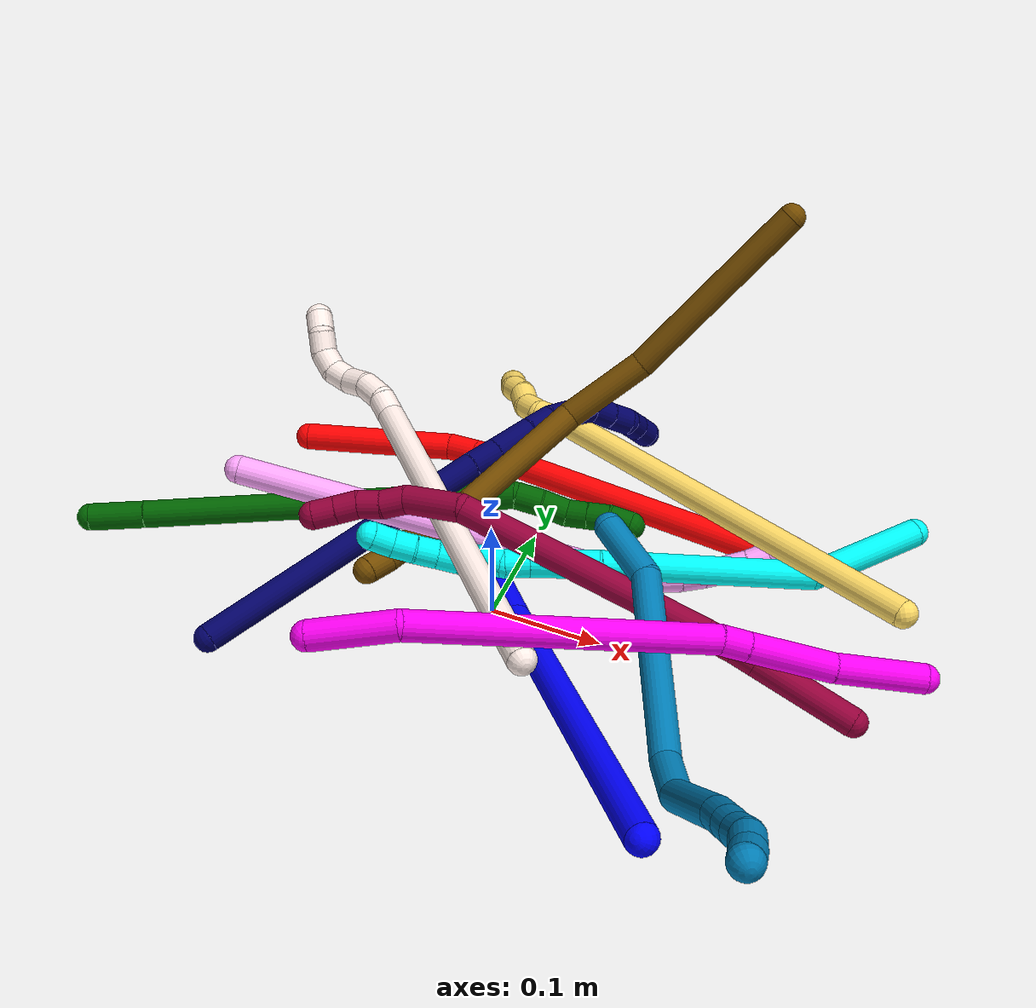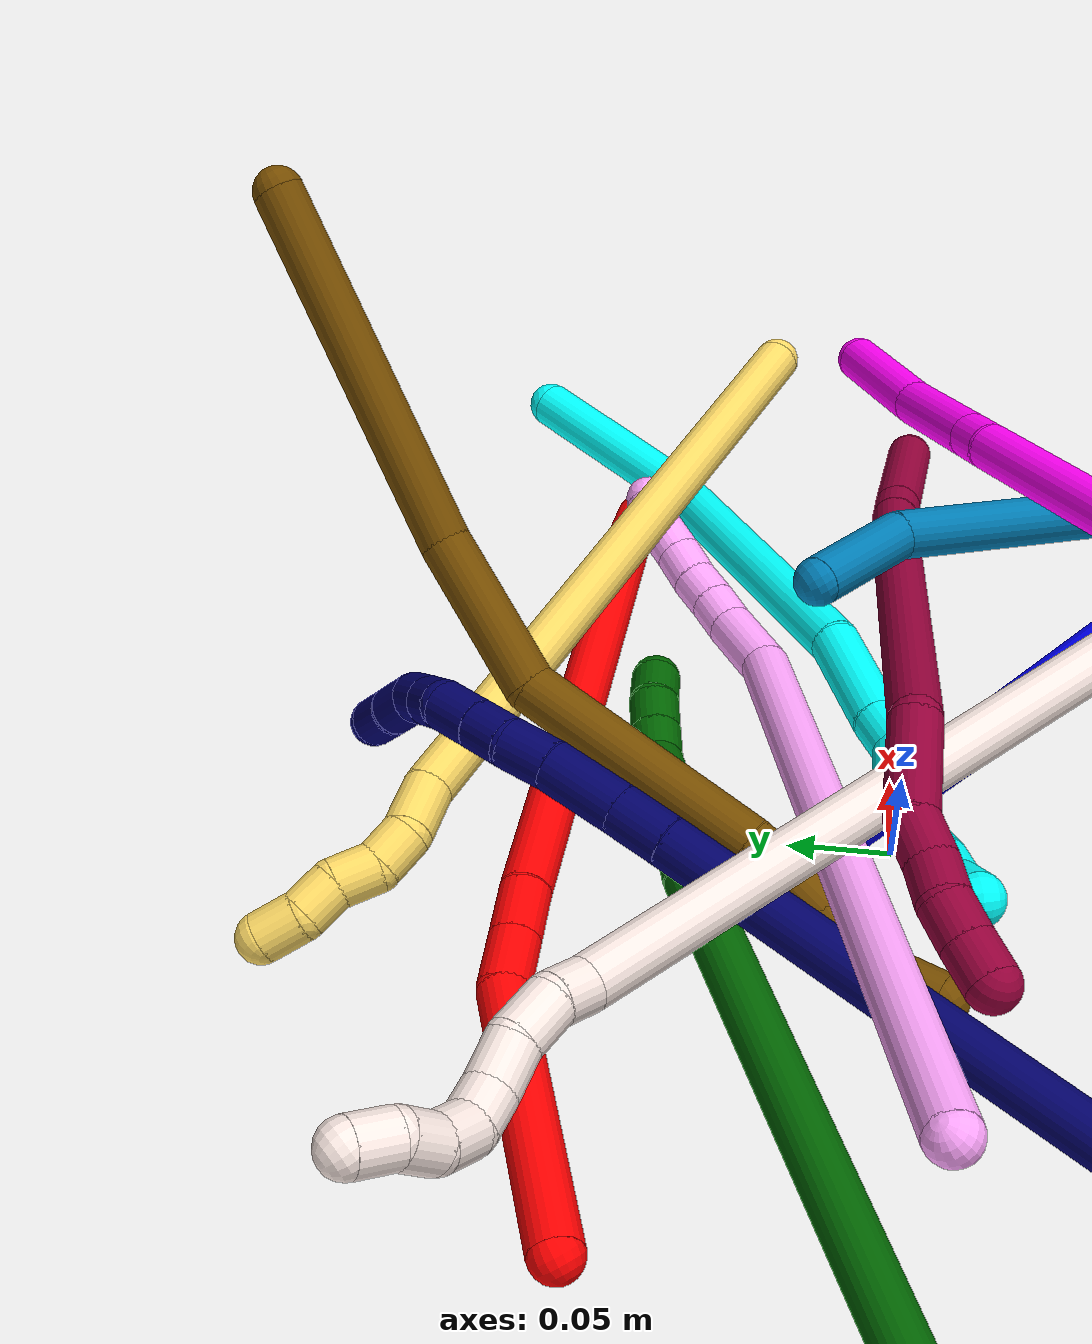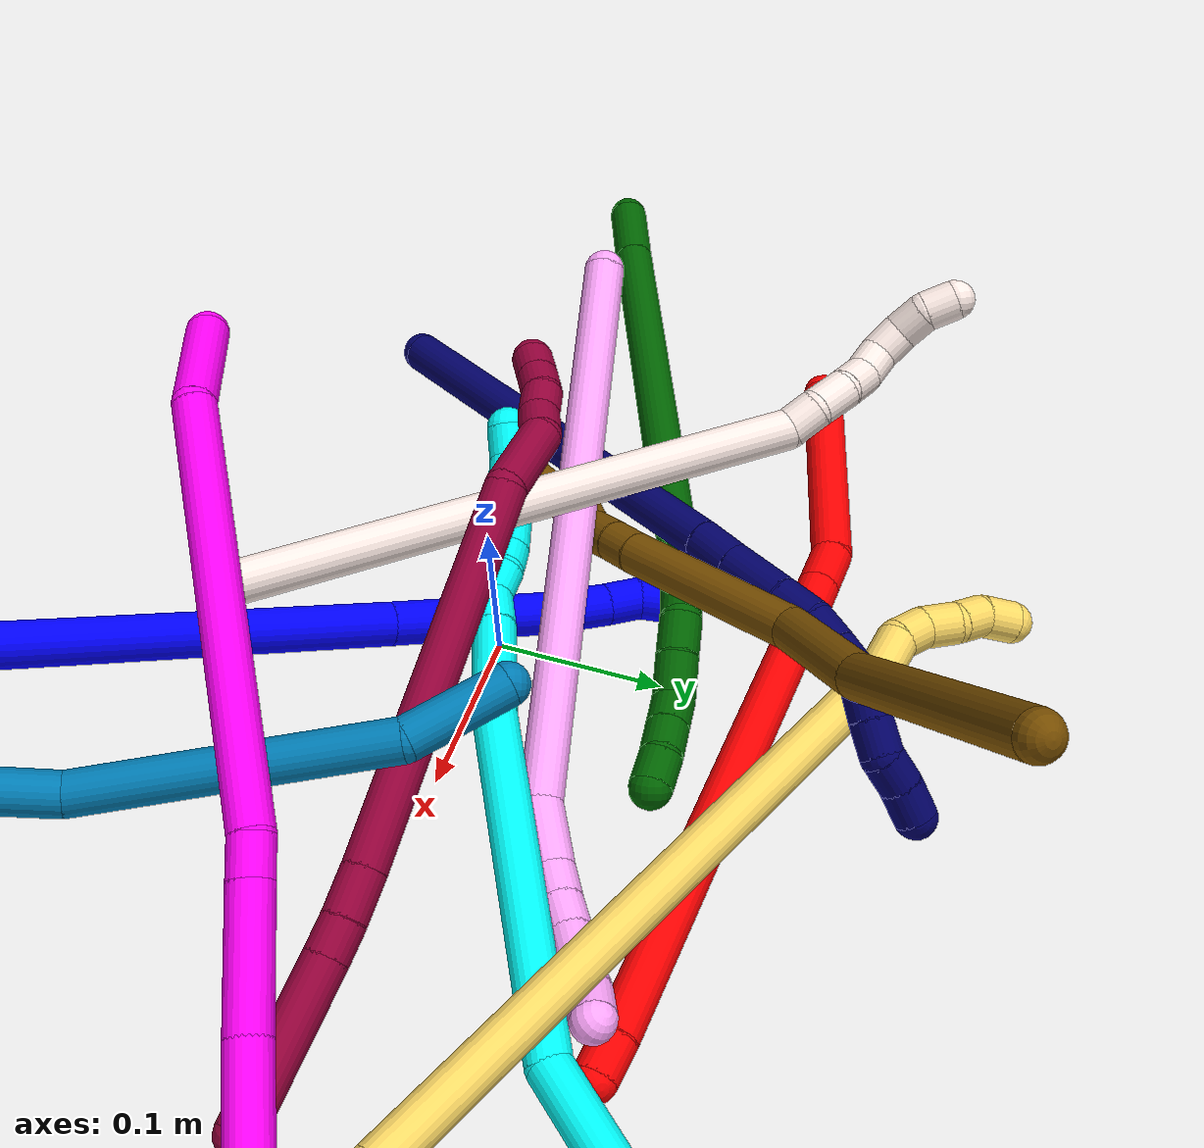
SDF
<sdf version="1.7">
 <world name="default">
  <plugin name="TubeGeneratorPlugin" filename="libtube_generator_plugin.so"/>
  <model name="photoneo_s_sensor">
   <static>1</static>
   <pose>0 0 2 1.57079 1.57079 3.14159</pose>
   <link name="link">
    <inertial><mass>0.1</mass></inertial>
    <sensor name="sensor" type="depth">
     <update_rate>30</update_rate>
     <camera>
      <horizontal_fov>1.22</horizontal_fov>
      <image><width>1920</width><height>1200</height><format>B8G8R8</format></image>
      <clip><near>0.1</near><far>4</far></clip>
      <depth_camera><output>points</output></depth_camera>
     </camera>
     <plugin name="camera_plugin" filename="libgazebo_ros_depth_camera.so">
      <baseline>0.2</baseline>
      <alwaysOn>1</alwaysOn>
      <updateRate>0.0</updateRate>
      <cameraName>camera_ir</cameraName>
      <imageTopicName>/camera/color/image_raw</imageTopicName>
      <cameraInfoTopicName>/camera/color/camera_info</cameraInfoTopicName>
      <depthImageTopicName>/camera/depth/image_raw</depthImageTopicName>
      <depthImageCameraInfoTopicName>/camera/depth/camera_info</depthImageCameraInfoTopicName>
      <pointCloudTopicName>/camera/depth/points</pointCloudTopicName>
      <frameName>fr_optical</frameName>
      <pointCloudCutoff>0.1</pointCloudCutoff>
      <pointCloudCutoffMax>2.0</pointCloudCutoffMax>
      <distortionK1>0</distortionK1>
      <distortionK2>0</distortionK2>
      <distortionK3>0</distortionK3>
      <distortionT1>0</distortionT1>
      <distortionT2>0</distortionT2>
      <CxPrime>0</CxPrime>
      <Cx>0</Cx>
      <Cy>0</Cy>
      <focalLength>0</focalLength>
      <hackBaseline>0</hackBaseline>
     </plugin>
    </sensor>
   </link>
  </model>
  <gravity>0 0 -9.8</gravity>
  <magnetic_field>6e-06 2.3e-05 -4.2e-05</magnetic_field>
  <atmosphere type="adiabatic"/>
  <physics name="default_physics" default="0" type="ode">
   <max_step_size>0.003</max_step_size>
   <real_time_factor>1</real_time_factor>
   <real_time_update_rate>1000</real_time_update_rate>
   <max_contacts>10000</max_contacts>
   <ode>
    <solver>
     <type>quick</type>
     <iters>100</iters>
     <sor>1.3</sor>
     <use_dynamic_moi_rescaling>0</use_dynamic_moi_rescaling>
    </solver>
    <constraints>
     <contact_max_correcting_vel>0</contact_max_correcting_vel>
     <contact_surface_layer>0.001</contact_surface_layer>
     <cfm>0</cfm>
     <erp>0.2</erp>
    </constraints>
   </ode>
  </physics>
  <scene><ambient>0.4 0.4 0.4 1</ambient><background>0.7 0.7 0.7 1</background><shadows>0</shadows></scene>
  <audio><device>default</device></audio>
  <spherical_coordinates>
   <surface_model>EARTH_WGS84</surface_model>
   <latitude_deg>0</latitude_deg>
   <longitude_deg>0</longitude_deg>
   <elevation>0</elevation>
   <heading_deg>0</heading_deg>
  </spherical_coordinates>
  <model name="bin">
   <static>1</static>
   <link name="bottom">
    <collision name="collision-bottom">
     <pose>0 0 -0.01 0 -0 0</pose>
     <geometry><box><size>0.8 0.6 0.02</size></box></geometry>
     <surface>
      <friction><ode><mu>100</mu><mu2>100</mu2></ode></friction>
      <contact><collide_bitmask>65535</collide_bitmask></contact>
     </surface>
    </collision>
   </link>
   <link name="west_wall">
    <collision name="collision-west_wall">
     <pose>-0.41 0 0.1 0 -0 0</pose>
     <geometry><box><size>0.02 0.6 0.2</size></box></geometry>
     <surface>
      <friction><ode><mu>100</mu><mu2>100</mu2></ode></friction>
      <contact><collide_bitmask>65535</collide_bitmask></contact>
     </surface>
    </collision>
   </link>
   <link name="east_wall">
    <collision name="collision-east_wall">
     <pose>0.41 0 0.1 0 -0 0</pose>
     <geometry><box><size>0.02 0.6 0.2</size></box></geometry>
     <surface>
      <friction><ode><mu>100</mu><mu2>100</mu2></ode></friction>
      <contact><collide_bitmask>65535</collide_bitmask></contact>
     </surface>
    </collision>
   </link>
   <link name="south_wall">
    <collision name="collision-south_wall">
     <pose>0 -0.31 0.1 0 -0 0</pose>
     <geometry><box><size>0.8 0.02 0.2</size></box></geometry>
     <surface>
      <friction><ode><mu>100</mu><mu2>100</mu2></ode></friction>
      <contact><collide_bitmask>65535</collide_bitmask></contact>
     </surface>
    </collision>
   </link>
   <link name="north_wall">
    <collision name="collision-north_wall">
     <pose>0 0.31 0.1 0 -0 0</pose>
     <geometry><box><size>0.8 0.02 0.2</size></box></geometry>
     <surface>
      <friction><ode><mu>100</mu><mu2>100</mu2></ode></friction>
      <contact><collide_bitmask>65535</collide_bitmask></contact>
     </surface>
    </collision>
   </link>
  </model>
  <model name="1">
   <static>0</static>
   <link name="1">
    <collision name="collision-cylinder-e_1_1_4">
     <pose>-0.069085 0.102384 -0.106049 -2.37377 -0.438271 1.00773</pose>
     <geometry><cylinder><radius>0.0125</radius><length>0.325587</length></cylinder></geometry>
     <surface>
      <friction><ode><mu>1.16</mu><mu2>1.16</mu2><slip1>0</slip1><slip2>0</slip2></ode></friction>
      <contact><ode><kp>1e+06</kp><kd>1</kd><max_vel>0</max_vel><min_depth>0.001</min_depth></ode></contact>
     </surface>
    </collision>
    <visual name="visual-cylinder-e_1_1_4">
     <pose>-0.069085 0.102384 -0.106049 -2.37377 -0.438271 1.00773</pose>
     <geometry><cylinder><radius>0.0125</radius><length>0.325587</length></cylinder></geometry>
     <material><ambient>0 0 1 1</ambient></material>
    </visual>
    <collision name="collision-cylinder-e_2_4_5">
     <pose>-0.157793 0.236407 -0.243176 -2.34729 -0.416544 0.933452</pose>
     <geometry><cylinder><radius>0.0125</radius><length>0.096993</length></cylinder></geometry>
     <surface>
      <friction><ode><mu>1.16</mu><mu2>1.16</mu2><slip1>0</slip1><slip2>0</slip2></ode></friction>
      <contact><ode><kp>1e+06</kp><kd>1</kd><max_vel>0</max_vel><min_depth>0.001</min_depth></ode></contact>
     </surface>
    </collision>
    <visual name="visual-cylinder-e_2_4_5">
     <pose>-0.157793 0.236407 -0.243176 -2.34729 -0.416544 0.933452</pose>
     <geometry><cylinder><radius>0.0125</radius><length>0.096993</length></cylinder></geometry>
     <material><ambient>0 0 1 1</ambient></material>
    </visual>
    <collision name="collision-cylinder-e_3_5_6">
     <pose>-0.184173 0.280966 -0.284482 -2.24031 -0.389235 0.773714</pose>
     <geometry><cylinder><radius>0.0125</radius><length>0.035621</length></cylinder></geometry>
     <surface>
      <friction><ode><mu>1.16</mu><mu2>1.16</mu2><slip1>0</slip1><slip2>0</slip2></ode></friction>
      <contact><ode><kp>1e+06</kp><kd>1</kd><max_vel>0</max_vel><min_depth>0.001</min_depth></ode></contact>
     </surface>
    </collision>
    <visual name="visual-cylinder-e_3_5_6">
     <pose>-0.184173 0.280966 -0.284482 -2.24031 -0.389235 0.773714</pose>
     <geometry><cylinder><radius>0.0125</radius><length>0.035621</length></cylinder></geometry>
     <material><ambient>0 0 1 1</ambient></material>
    </visual>
    <collision name="collision-cylinder-e_4_6_7">
     <pose>-0.194814 0.302154 -0.300499 -2.18177 -0.367187 0.685339</pose>
     <geometry><cylinder><radius>0.0125</radius><length>0.021628</length></cylinder></geometry>
     <surface>
      <friction><ode><mu>1.16</mu><mu2>1.16</mu2><slip1>0</slip1><slip2>0</slip2></ode></friction>
      <contact><ode><kp>1e+06</kp><kd>1</kd><max_vel>0</max_vel><min_depth>0.001</min_depth></ode></contact>
     </surface>
    </collision>
    <visual name="visual-cylinder-e_4_6_7">
     <pose>-0.194814 0.302154 -0.300499 -2.18177 -0.367187 0.685339</pose>
     <geometry><cylinder><radius>0.0125</radius><length>0.021628</length></cylinder></geometry>
     <material><ambient>0 0 1 1</ambient></material>
    </visual>
    <collision name="collision-cylinder-e_5_7_2">
     <pose>-0.197733 0.317568 -0.31334 -2.34949 0.095664 -0.227964</pose>
     <geometry><cylinder><radius>0.0125</radius><length>0.020171</length></cylinder></geometry>
     <surface>
      <friction><ode><mu>1.16</mu><mu2>1.16</mu2><slip1>0</slip1><slip2>0</slip2></ode></friction>
      <contact><ode><kp>1e+06</kp><kd>1</kd><max_vel>0</max_vel><min_depth>0.001</min_depth></ode></contact>
     </surface>
    </collision>
    <visual name="visual-cylinder-e_5_7_2">
     <pose>-0.197733 0.317568 -0.31334 -2.34949 0.095664 -0.227964</pose>
     <geometry><cylinder><radius>0.0125</radius><length>0.020171</length></cylinder></geometry>
     <material><ambient>0 0 1 1</ambient></material>
    </visual>
    <collision name="collision-sphere-2">
     <pose>-0.196769 0.324714 -0.320392 0 -0 0</pose>
     <geometry><sphere><radius>0.0125</radius></sphere></geometry>
     <surface>
      <friction><ode><mu>1.16</mu><mu2>1.16</mu2><slip1>0</slip1><slip2>0</slip2></ode></friction>
      <contact><ode><kp>1e+06</kp><kd>1</kd><max_vel>0</max_vel><min_depth>0.001</min_depth></ode></contact>
     </surface>
    </collision>
    <visual name="visual-sphere-2">
     <pose>-0.196769 0.324714 -0.320392 0 -0 0</pose>
     <geometry><sphere><radius>0.0125</radius></sphere></geometry>
     <material><ambient>0 0 1 1</ambient></material>
    </visual>
    <collision name="collision-sphere-7">
     <pose>-0.198696 0.310421 -0.306289 0 -0 0</pose>
     <geometry><sphere><radius>0.0125</radius></sphere></geometry>
     <surface>
      <friction><ode><mu>1.16</mu><mu2>1.16</mu2><slip1>0</slip1><slip2>0</slip2></ode></friction>
      <contact><ode><kp>1e+06</kp><kd>1</kd><max_vel>0</max_vel><min_depth>0.001</min_depth></ode></contact>
     </surface>
    </collision>
    <visual name="visual-sphere-7">
     <pose>-0.198696 0.310421 -0.306289 0 -0 0</pose>
     <geometry><sphere><radius>0.0125</radius></sphere></geometry>
     <material><ambient>0 0 1 1</ambient></material>
    </visual>
    <collision name="collision-sphere-6">
     <pose>-0.190932 0.293887 -0.294709 0 -0 0</pose>
     <geometry><sphere><radius>0.0125</radius></sphere></geometry>
     <surface>
      <friction><ode><mu>1.16</mu><mu2>1.16</mu2><slip1>0</slip1><slip2>0</slip2></ode></friction>
      <contact><ode><kp>1e+06</kp><kd>1</kd><max_vel>0</max_vel><min_depth>0.001</min_depth></ode></contact>
     </surface>
    </collision>
    <visual name="visual-sphere-6">
     <pose>-0.190932 0.293887 -0.294709 0 -0 0</pose>
     <geometry><sphere><radius>0.0125</radius></sphere></geometry>
     <material><ambient>0 0 1 1</ambient></material>
    </visual>
    <collision name="collision-sphere-5">
     <pose>-0.177414 0.268045 -0.274256 0 -0 0</pose>
     <geometry><sphere><radius>0.0125</radius></sphere></geometry>
     <surface>
      <friction><ode><mu>1.16</mu><mu2>1.16</mu2><slip1>0</slip1><slip2>0</slip2></ode></friction>
      <contact><ode><kp>1e+06</kp><kd>1</kd><max_vel>0</max_vel><min_depth>0.001</min_depth></ode></contact>
     </surface>
    </collision>
    <visual name="visual-sphere-5">
     <pose>-0.177414 0.268045 -0.274256 0 -0 0</pose>
     <geometry><sphere><radius>0.0125</radius></sphere></geometry>
     <material><ambient>0 0 1 1</ambient></material>
    </visual>
    <collision name="collision-sphere-1">
     <geometry><sphere><radius>0.0125</radius></sphere></geometry>
     <surface>
      <friction><ode><mu>1.16</mu><mu2>1.16</mu2><slip1>0</slip1><slip2>0</slip2></ode></friction>
      <contact><ode><kp>1e+06</kp><kd>1</kd><max_vel>0</max_vel><min_depth>0.001</min_depth></ode></contact>
     </surface>
    </collision>
    <visual name="visual-sphere-1">
     <geometry><sphere><radius>0.0125</radius></sphere></geometry>
     <material><ambient>0 0 1 1</ambient></material>
    </visual>
    <collision name="collision-sphere-4">
     <pose>-0.138171 0.204769 -0.212097 0 -0 0</pose>
     <geometry><sphere><radius>0.0125</radius></sphere></geometry>
     <surface>
      <friction><ode><mu>1.16</mu><mu2>1.16</mu2><slip1>0</slip1><slip2>0</slip2></ode></friction>
      <contact><ode><kp>1e+06</kp><kd>1</kd><max_vel>0</max_vel><min_depth>0.001</min_depth></ode></contact>
     </surface>
    </collision>
    <visual name="visual-sphere-4">
     <pose>-0.138171 0.204769 -0.212097 0 -0 0</pose>
     <geometry><sphere><radius>0.0125</radius></sphere></geometry>
     <material><ambient>0 0 1 1</ambient></material>
    </visual>
    <inertial>
     <pose>-0.105121 0.158428 -0.162135 0 -0 0</pose>
     <mass>0.5</mass>
     <inertia>
      <ixx>0.003705</ixx>
      <ixy>0</ixy>
      <ixz>0</ixz>
      <iyy>0.001893</iyy>
      <iyz>0</iyz>
      <izz>-0.000639</izz>
     </inertia>
    </inertial>
   </link>
   <pose>0.228961 -0.288502 0.164075 0.627675 -0.486212 0.333135</pose>
  </model>
  <model name="2">
   <static>0</static>
   <link name="2">
    <collision name="collision-cylinder-e_1_1_4">
     <pose>-0.010004 -0.00013 0.005987 0.021658 -1.03143 -0.012278</pose>
     <geometry><cylinder><radius>0.0125</radius><length>0.02332</length></cylinder></geometry>
     <surface>
      <friction><ode><mu>1.16</mu><mu2>1.16</mu2><slip1>0</slip1><slip2>0</slip2></ode></friction>
      <contact><ode><kp>1e+06</kp><kd>1</kd><max_vel>0</max_vel><min_depth>0.001</min_depth></ode></contact>
     </surface>
    </collision>
    <visual name="visual-cylinder-e_1_1_4">
     <pose>-0.010004 -0.00013 0.005987 0.021658 -1.03143 -0.012278</pose>
     <geometry><cylinder><radius>0.0125</radius><length>0.02332</length></cylinder></geometry>
     <material><ambient>1 0 0 1</ambient></material>
    </visual>
    <collision name="collision-cylinder-e_2_4_5">
     <pose>-0.135455 -0.000983 0.093216 0.008907 -0.957558 -0.004624</pose>
     <geometry><cylinder><radius>0.0125</radius><length>0.282338</length></cylinder></geometry>
     <surface>
      <friction><ode><mu>1.16</mu><mu2>1.16</mu2><slip1>0</slip1><slip2>0</slip2></ode></friction>
      <contact><ode><kp>1e+06</kp><kd>1</kd><max_vel>0</max_vel><min_depth>0.001</min_depth></ode></contact>
     </surface>
    </collision>
    <visual name="visual-cylinder-e_2_4_5">
     <pose>-0.135455 -0.000983 0.093216 0.008907 -0.957558 -0.004624</pose>
     <geometry><cylinder><radius>0.0125</radius><length>0.282338</length></cylinder></geometry>
     <material><ambient>1 0 0 1</ambient></material>
    </visual>
    <collision name="collision-cylinder-e_3_5_6">
     <pose>-0.261729 -0.002444 0.183689 0.079695 -0.863233 -0.036721</pose>
     <geometry><cylinder><radius>0.0125</radius><length>0.028495</length></cylinder></geometry>
     <surface>
      <friction><ode><mu>1.16</mu><mu2>1.16</mu2><slip1>0</slip1><slip2>0</slip2></ode></friction>
      <contact><ode><kp>1e+06</kp><kd>1</kd><max_vel>0</max_vel><min_depth>0.001</min_depth></ode></contact>
     </surface>
    </collision>
    <visual name="visual-cylinder-e_3_5_6">
     <pose>-0.261729 -0.002444 0.183689 0.079695 -0.863233 -0.036721</pose>
     <geometry><cylinder><radius>0.0125</radius><length>0.028495</length></cylinder></geometry>
     <material><ambient>1 0 0 1</ambient></material>
    </visual>
    <collision name="collision-cylinder-e_4_6_7">
     <pose>-0.283307 -0.003819 0.201951 0.070475 -0.870917 -0.032799</pose>
     <geometry><cylinder><radius>0.0125</radius><length>0.028109</length></cylinder></geometry>
     <surface>
      <friction><ode><mu>1.16</mu><mu2>1.16</mu2><slip1>0</slip1><slip2>0</slip2></ode></friction>
      <contact><ode><kp>1e+06</kp><kd>1</kd><max_vel>0</max_vel><min_depth>0.001</min_depth></ode></contact>
     </surface>
    </collision>
    <visual name="visual-cylinder-e_4_6_7">
     <pose>-0.283307 -0.003819 0.201951 0.070475 -0.870917 -0.032799</pose>
     <geometry><cylinder><radius>0.0125</radius><length>0.028109</length></cylinder></geometry>
     <material><ambient>1 0 0 1</ambient></material>
    </visual>
    <collision name="collision-cylinder-e_5_7_2">
     <pose>-0.336003 0.01205 0.26305 -0.306984 -0.654873 0.105001</pose>
     <geometry><cylinder><radius>0.0125</radius><length>0.137739</length></cylinder></geometry>
     <surface>
      <friction><ode><mu>1.16</mu><mu2>1.16</mu2><slip1>0</slip1><slip2>0</slip2></ode></friction>
      <contact><ode><kp>1e+06</kp><kd>1</kd><max_vel>0</max_vel><min_depth>0.001</min_depth></ode></contact>
     </surface>
    </collision>
    <visual name="visual-cylinder-e_5_7_2">
     <pose>-0.336003 0.01205 0.26305 -0.306984 -0.654873 0.105001</pose>
     <geometry><cylinder><radius>0.0125</radius><length>0.137739</length></cylinder></geometry>
     <material><ambient>1 0 0 1</ambient></material>
    </visual>
    <collision name="collision-sphere-2">
     <pose>-0.377948 0.028556 0.315118 0 -0 0</pose>
     <geometry><sphere><radius>0.0125</radius></sphere></geometry>
     <surface>
      <friction><ode><mu>1.16</mu><mu2>1.16</mu2><slip1>0</slip1><slip2>0</slip2></ode></friction>
      <contact><ode><kp>1e+06</kp><kd>1</kd><max_vel>0</max_vel><min_depth>0.001</min_depth></ode></contact>
     </surface>
    </collision>
    <visual name="visual-sphere-2">
     <pose>-0.377948 0.028556 0.315118 0 -0 0</pose>
     <geometry><sphere><radius>0.0125</radius></sphere></geometry>
     <material><ambient>1 0 0 1</ambient></material>
    </visual>
    <collision name="collision-sphere-7">
     <pose>-0.294057 -0.004456 0.210981 0 -0 0</pose>
     <geometry><sphere><radius>0.0125</radius></sphere></geometry>
     <surface>
      <friction><ode><mu>1.16</mu><mu2>1.16</mu2><slip1>0</slip1><slip2>0</slip2></ode></friction>
      <contact><ode><kp>1e+06</kp><kd>1</kd><max_vel>0</max_vel><min_depth>0.001</min_depth></ode></contact>
     </surface>
    </collision>
    <visual name="visual-sphere-7">
     <pose>-0.294057 -0.004456 0.210981 0 -0 0</pose>
     <geometry><sphere><radius>0.0125</radius></sphere></geometry>
     <material><ambient>1 0 0 1</ambient></material>
    </visual>
    <collision name="collision-sphere-6">
     <pose>-0.272556 -0.003181 0.192921 0 -0 0</pose>
     <geometry><sphere><radius>0.0125</radius></sphere></geometry>
     <surface>
      <friction><ode><mu>1.16</mu><mu2>1.16</mu2><slip1>0</slip1><slip2>0</slip2></ode></friction>
      <contact><ode><kp>1e+06</kp><kd>1</kd><max_vel>0</max_vel><min_depth>0.001</min_depth></ode></contact>
     </surface>
    </collision>
    <visual name="visual-sphere-6">
     <pose>-0.272556 -0.003181 0.192921 0 -0 0</pose>
     <geometry><sphere><radius>0.0125</radius></sphere></geometry>
     <material><ambient>1 0 0 1</ambient></material>
    </visual>
    <collision name="collision-sphere-5">
     <pose>-0.250901 -0.001707 0.174458 0 -0 0</pose>
     <geometry><sphere><radius>0.0125</radius></sphere></geometry>
     <surface>
      <friction><ode><mu>1.16</mu><mu2>1.16</mu2><slip1>0</slip1><slip2>0</slip2></ode></friction>
      <contact><ode><kp>1e+06</kp><kd>1</kd><max_vel>0</max_vel><min_depth>0.001</min_depth></ode></contact>
     </surface>
    </collision>
    <visual name="visual-sphere-5">
     <pose>-0.250901 -0.001707 0.174458 0 -0 0</pose>
     <geometry><sphere><radius>0.0125</radius></sphere></geometry>
     <material><ambient>1 0 0 1</ambient></material>
    </visual>
    <collision name="collision-sphere-1">
     <geometry><sphere><radius>0.0125</radius></sphere></geometry>
     <surface>
      <friction><ode><mu>1.16</mu><mu2>1.16</mu2><slip1>0</slip1><slip2>0</slip2></ode></friction>
      <contact><ode><kp>1e+06</kp><kd>1</kd><max_vel>0</max_vel><min_depth>0.001</min_depth></ode></contact>
     </surface>
    </collision>
    <visual name="visual-sphere-1">
     <geometry><sphere><radius>0.0125</radius></sphere></geometry>
     <material><ambient>1 0 0 1</ambient></material>
    </visual>
    <collision name="collision-sphere-4">
     <pose>-0.020009 -0.000259 0.011974 0 -0 0</pose>
     <geometry><sphere><radius>0.0125</radius></sphere></geometry>
     <surface>
      <friction><ode><mu>1.16</mu><mu2>1.16</mu2><slip1>0</slip1><slip2>0</slip2></ode></friction>
      <contact><ode><kp>1e+06</kp><kd>1</kd><max_vel>0</max_vel><min_depth>0.001</min_depth></ode></contact>
     </surface>
    </collision>
    <visual name="visual-sphere-4">
     <pose>-0.020009 -0.000259 0.011974 0 -0 0</pose>
     <geometry><sphere><radius>0.0125</radius></sphere></geometry>
     <material><ambient>1 0 0 1</ambient></material>
    </visual>
    <inertial>
     <pose>-0.200359 0.002404 0.147202 0 -0 0</pose>
     <mass>0.5</mass>
     <inertia>
      <ixx>0.00125</ixx>
      <ixy>0</ixy>
      <ixz>0</ixz>
      <iyy>0.002126</iyy>
      <iyz>0</iyz>
      <izz>0.001666</izz>
     </inertia>
    </inertial>
   </link>
   <pose>0.243999 0.14398 0.011484 2.22919 0.425446 -0.55017</pose>
  </model>
  <model name="3">
   <static>0</static>
   <link name="3">
    <collision name="collision-cylinder-e_1_1_4">
     <pose>-0.042104 -0.005809 -0.032391 2.96414 -0.907389 -2.7807</pose>
     <geometry><cylinder><radius>0.0125</radius><length>0.106877</length></cylinder></geometry>
     <surface>
      <friction><ode><mu>1.16</mu><mu2>1.16</mu2><slip1>0</slip1><slip2>0</slip2></ode></friction>
      <contact><ode><kp>1e+06</kp><kd>1</kd><max_vel>0</max_vel><min_depth>0.001</min_depth></ode></contact>
     </surface>
    </collision>
    <visual name="visual-cylinder-e_1_1_4">
     <pose>-0.042104 -0.005809 -0.032391 2.96414 -0.907389 -2.7807</pose>
     <geometry><cylinder><radius>0.0125</radius><length>0.106877</length></cylinder></geometry>
     <material><ambient>0.003922 1 0.996078 1</ambient></material>
    </visual>
    <collision name="collision-cylinder-e_2_4_5">
     <pose>-0.169185 -0.047009 -0.09228 2.23135 -1.08545 -1.77828</pose>
     <geometry><cylinder><radius>0.0125</radius><length>0.192143</length></cylinder></geometry>
     <surface>
      <friction><ode><mu>1.16</mu><mu2>1.16</mu2><slip1>0</slip1><slip2>0</slip2></ode></friction>
      <contact><ode><kp>1e+06</kp><kd>1</kd><max_vel>0</max_vel><min_depth>0.001</min_depth></ode></contact>
     </surface>
    </collision>
    <visual name="visual-cylinder-e_2_4_5">
     <pose>-0.169185 -0.047009 -0.09228 2.23135 -1.08545 -1.77828</pose>
     <geometry><cylinder><radius>0.0125</radius><length>0.192143</length></cylinder></geometry>
     <material><ambient>0.003922 1 0.996078 1</ambient></material>
    </visual>
    <collision name="collision-cylinder-e_3_5_6">
     <pose>-0.282561 -0.088749 -0.124495 2.20971 -1.2992 -1.97201</pose>
     <geometry><cylinder><radius>0.0125</radius><length>0.058959</length></cylinder></geometry>
     <surface>
      <friction><ode><mu>1.16</mu><mu2>1.16</mu2><slip1>0</slip1><slip2>0</slip2></ode></friction>
      <contact><ode><kp>1e+06</kp><kd>1</kd><max_vel>0</max_vel><min_depth>0.001</min_depth></ode></contact>
     </surface>
    </collision>
    <visual name="visual-cylinder-e_3_5_6">
     <pose>-0.282561 -0.088749 -0.124495 2.20971 -1.2992 -1.97201</pose>
     <geometry><cylinder><radius>0.0125</radius><length>0.058959</length></cylinder></geometry>
     <material><ambient>0.003922 1 0.996078 1</ambient></material>
    </visual>
    <collision name="collision-cylinder-e_4_6_7">
     <pose>-0.321306 -0.097543 -0.131995 2.4208 -1.22684 -2.15864</pose>
     <geometry><cylinder><radius>0.0125</radius><length>0.021981</length></cylinder></geometry>
     <surface>
      <friction><ode><mu>1.16</mu><mu2>1.16</mu2><slip1>0</slip1><slip2>0</slip2></ode></friction>
      <contact><ode><kp>1e+06</kp><kd>1</kd><max_vel>0</max_vel><min_depth>0.001</min_depth></ode></contact>
     </surface>
    </collision>
    <visual name="visual-cylinder-e_4_6_7">
     <pose>-0.321306 -0.097543 -0.131995 2.4208 -1.22684 -2.15864</pose>
     <geometry><cylinder><radius>0.0125</radius><length>0.021981</length></cylinder></geometry>
     <material><ambient>0.003922 1 0.996078 1</ambient></material>
    </visual>
    <collision name="collision-cylinder-e_5_7_8">
     <pose>-0.341333 -0.101812 -0.133043 0.809394 -1.31631 -0.639607</pose>
     <geometry><cylinder><radius>0.0125</radius><length>0.020004</length></cylinder></geometry>
     <surface>
      <friction><ode><mu>1.16</mu><mu2>1.16</mu2><slip1>0</slip1><slip2>0</slip2></ode></friction>
      <contact><ode><kp>1e+06</kp><kd>1</kd><max_vel>0</max_vel><min_depth>0.001</min_depth></ode></contact>
     </surface>
    </collision>
    <visual name="visual-cylinder-e_5_7_8">
     <pose>-0.341333 -0.101812 -0.133043 0.809394 -1.31631 -0.639607</pose>
     <geometry><cylinder><radius>0.0125</radius><length>0.020004</length></cylinder></geometry>
     <material><ambient>0.003922 1 0.996078 1</ambient></material>
    </visual>
    <collision name="collision-cylinder-e_6_8_9">
     <pose>-0.361018 -0.103352 -0.131238 -1.33773 -1.54178 1.30959</pose>
     <geometry><cylinder><radius>0.0125</radius><length>0.020021</length></cylinder></geometry>
     <surface>
      <friction><ode><mu>1.16</mu><mu2>1.16</mu2><slip1>0</slip1><slip2>0</slip2></ode></friction>
      <contact><ode><kp>1e+06</kp><kd>1</kd><max_vel>0</max_vel><min_depth>0.001</min_depth></ode></contact>
     </surface>
    </collision>
    <visual name="visual-cylinder-e_6_8_9">
     <pose>-0.361018 -0.103352 -0.131238 -1.33773 -1.54178 1.30959</pose>
     <geometry><cylinder><radius>0.0125</radius><length>0.020021</length></cylinder></geometry>
     <material><ambient>0.003922 1 0.996078 1</ambient></material>
    </visual>
    <collision name="collision-cylinder-e_7_9_10">
     <pose>-0.380119 -0.107195 -0.131782 1.7177 -1.14087 -1.27866</pose>
     <geometry><cylinder><radius>0.0125</radius><length>0.020009</length></cylinder></geometry>
     <surface>
      <friction><ode><mu>1.16</mu><mu2>1.16</mu2><slip1>0</slip1><slip2>0</slip2></ode></friction>
      <contact><ode><kp>1e+06</kp><kd>1</kd><max_vel>0</max_vel><min_depth>0.001</min_depth></ode></contact>
     </surface>
    </collision>
    <visual name="visual-cylinder-e_7_9_10">
     <pose>-0.380119 -0.107195 -0.131782 1.7177 -1.14087 -1.27866</pose>
     <geometry><cylinder><radius>0.0125</radius><length>0.020009</length></cylinder></geometry>
     <material><ambient>0.003922 1 0.996078 1</ambient></material>
    </visual>
    <collision name="collision-cylinder-e_8_10_11">
     <pose>-0.397585 -0.116427 -0.134353 1.93732 -0.991975 -1.33392</pose>
     <geometry><cylinder><radius>0.0125</radius><length>0.020003</length></cylinder></geometry>
     <surface>
      <friction><ode><mu>1.16</mu><mu2>1.16</mu2><slip1>0</slip1><slip2>0</slip2></ode></friction>
      <contact><ode><kp>1e+06</kp><kd>1</kd><max_vel>0</max_vel><min_depth>0.001</min_depth></ode></contact>
     </surface>
    </collision>
    <visual name="visual-cylinder-e_8_10_11">
     <pose>-0.397585 -0.116427 -0.134353 1.93732 -0.991975 -1.33392</pose>
     <geometry><cylinder><radius>0.0125</radius><length>0.020003</length></cylinder></geometry>
     <material><ambient>0.003922 1 0.996078 1</ambient></material>
    </visual>
    <collision name="collision-cylinder-e_9_11_12">
     <pose>-0.41484 -0.126064 -0.137097 1.74205 -1.09331 -1.25171</pose>
     <geometry><cylinder><radius>0.0125</radius><length>0.020001</length></cylinder></geometry>
     <surface>
      <friction><ode><mu>1.16</mu><mu2>1.16</mu2><slip1>0</slip1><slip2>0</slip2></ode></friction>
      <contact><ode><kp>1e+06</kp><kd>1</kd><max_vel>0</max_vel><min_depth>0.001</min_depth></ode></contact>
     </surface>
    </collision>
    <visual name="visual-cylinder-e_9_11_12">
     <pose>-0.41484 -0.126064 -0.137097 1.74205 -1.09331 -1.25171</pose>
     <geometry><cylinder><radius>0.0125</radius><length>0.020001</length></cylinder></geometry>
     <material><ambient>0.003922 1 0.996078 1</ambient></material>
    </visual>
    <collision name="collision-cylinder-e_10_12_2">
     <pose>-0.431039 -0.137089 -0.139948 1.87907 -0.820684 -1.0736</pose>
     <geometry><cylinder><radius>0.0125</radius><length>0.020002</length></cylinder></geometry>
     <surface>
      <friction><ode><mu>1.16</mu><mu2>1.16</mu2><slip1>0</slip1><slip2>0</slip2></ode></friction>
      <contact><ode><kp>1e+06</kp><kd>1</kd><max_vel>0</max_vel><min_depth>0.001</min_depth></ode></contact>
     </surface>
    </collision>
    <visual name="visual-cylinder-e_10_12_2">
     <pose>-0.431039 -0.137089 -0.139948 1.87907 -0.820684 -1.0736</pose>
     <geometry><cylinder><radius>0.0125</radius><length>0.020002</length></cylinder></geometry>
     <material><ambient>0.003922 1 0.996078 1</ambient></material>
    </visual>
    <collision name="collision-sphere-2">
     <pose>-0.438355 -0.143585 -0.142017 0 -0 0</pose>
     <geometry><sphere><radius>0.0125</radius></sphere></geometry>
     <surface>
      <friction><ode><mu>1.16</mu><mu2>1.16</mu2><slip1>0</slip1><slip2>0</slip2></ode></friction>
      <contact><ode><kp>1e+06</kp><kd>1</kd><max_vel>0</max_vel><min_depth>0.001</min_depth></ode></contact>
     </surface>
    </collision>
    <visual name="visual-sphere-2">
     <pose>-0.438355 -0.143585 -0.142017 0 -0 0</pose>
     <geometry><sphere><radius>0.0125</radius></sphere></geometry>
     <material><ambient>0.003922 1 0.996078 1</ambient></material>
    </visual>
    <collision name="collision-sphere-12">
     <pose>-0.423722 -0.130592 -0.13788 0 -0 0</pose>
     <geometry><sphere><radius>0.0125</radius></sphere></geometry>
     <surface>
      <friction><ode><mu>1.16</mu><mu2>1.16</mu2><slip1>0</slip1><slip2>0</slip2></ode></friction>
      <contact><ode><kp>1e+06</kp><kd>1</kd><max_vel>0</max_vel><min_depth>0.001</min_depth></ode></contact>
     </surface>
    </collision>
    <visual name="visual-sphere-12">
     <pose>-0.423722 -0.130592 -0.13788 0 -0 0</pose>
     <geometry><sphere><radius>0.0125</radius></sphere></geometry>
     <material><ambient>0.003922 1 0.996078 1</ambient></material>
    </visual>
    <collision name="collision-sphere-11">
     <pose>-0.405958 -0.121535 -0.136313 0 -0 0</pose>
     <geometry><sphere><radius>0.0125</radius></sphere></geometry>
     <surface>
      <friction><ode><mu>1.16</mu><mu2>1.16</mu2><slip1>0</slip1><slip2>0</slip2></ode></friction>
      <contact><ode><kp>1e+06</kp><kd>1</kd><max_vel>0</max_vel><min_depth>0.001</min_depth></ode></contact>
     </surface>
    </collision>
    <visual name="visual-sphere-11">
     <pose>-0.405958 -0.121535 -0.136313 0 -0 0</pose>
     <geometry><sphere><radius>0.0125</radius></sphere></geometry>
     <material><ambient>0.003922 1 0.996078 1</ambient></material>
    </visual>
    <collision name="collision-sphere-10">
     <pose>-0.389213 -0.11132 -0.132392 0 -0 0</pose>
     <geometry><sphere><radius>0.0125</radius></sphere></geometry>
     <surface>
      <friction><ode><mu>1.16</mu><mu2>1.16</mu2><slip1>0</slip1><slip2>0</slip2></ode></friction>
      <contact><ode><kp>1e+06</kp><kd>1</kd><max_vel>0</max_vel><min_depth>0.001</min_depth></ode></contact>
     </surface>
    </collision>
    <visual name="visual-sphere-10">
     <pose>-0.389213 -0.11132 -0.132392 0 -0 0</pose>
     <geometry><sphere><radius>0.0125</radius></sphere></geometry>
     <material><ambient>0.003922 1 0.996078 1</ambient></material>
    </visual>
    <collision name="collision-sphere-9">
     <pose>-0.371024 -0.103069 -0.131171 0 -0 0</pose>
     <geometry><sphere><radius>0.0125</radius></sphere></geometry>
     <surface>
      <friction><ode><mu>1.16</mu><mu2>1.16</mu2><slip1>0</slip1><slip2>0</slip2></ode></friction>
      <contact><ode><kp>1e+06</kp><kd>1</kd><max_vel>0</max_vel><min_depth>0.001</min_depth></ode></contact>
     </surface>
    </collision>
    <visual name="visual-sphere-9">
     <pose>-0.371024 -0.103069 -0.131171 0 -0 0</pose>
     <geometry><sphere><radius>0.0125</radius></sphere></geometry>
     <material><ambient>0.003922 1 0.996078 1</ambient></material>
    </visual>
    <collision name="collision-sphere-4">
     <pose>-0.084208 -0.011618 -0.064782 0 -0 0</pose>
     <geometry><sphere><radius>0.0125</radius></sphere></geometry>
     <surface>
      <friction><ode><mu>1.16</mu><mu2>1.16</mu2><slip1>0</slip1><slip2>0</slip2></ode></friction>
      <contact><ode><kp>1e+06</kp><kd>1</kd><max_vel>0</max_vel><min_depth>0.001</min_depth></ode></contact>
     </surface>
    </collision>
    <visual name="visual-sphere-4">
     <pose>-0.084208 -0.011618 -0.064782 0 -0 0</pose>
     <geometry><sphere><radius>0.0125</radius></sphere></geometry>
     <material><ambient>0.003922 1 0.996078 1</ambient></material>
    </visual>
    <collision name="collision-sphere-1">
     <geometry><sphere><radius>0.0125</radius></sphere></geometry>
     <surface>
      <friction><ode><mu>1.16</mu><mu2>1.16</mu2><slip1>0</slip1><slip2>0</slip2></ode></friction>
      <contact><ode><kp>1e+06</kp><kd>1</kd><max_vel>0</max_vel><min_depth>0.001</min_depth></ode></contact>
     </surface>
    </collision>
    <visual name="visual-sphere-1">
     <geometry><sphere><radius>0.0125</radius></sphere></geometry>
     <material><ambient>0.003922 1 0.996078 1</ambient></material>
    </visual>
    <collision name="collision-sphere-8">
     <pose>-0.351012 -0.103635 -0.131305 0 -0 0</pose>
     <geometry><sphere><radius>0.0125</radius></sphere></geometry>
     <surface>
      <friction><ode><mu>1.16</mu><mu2>1.16</mu2><slip1>0</slip1><slip2>0</slip2></ode></friction>
      <contact><ode><kp>1e+06</kp><kd>1</kd><max_vel>0</max_vel><min_depth>0.001</min_depth></ode></contact>
     </surface>
    </collision>
    <visual name="visual-sphere-8">
     <pose>-0.351012 -0.103635 -0.131305 0 -0 0</pose>
     <geometry><sphere><radius>0.0125</radius></sphere></geometry>
     <material><ambient>0.003922 1 0.996078 1</ambient></material>
    </visual>
    <collision name="collision-sphere-5">
     <pose>-0.254161 -0.0824 -0.119779 0 -0 0</pose>
     <geometry><sphere><radius>0.0125</radius></sphere></geometry>
     <surface>
      <friction><ode><mu>1.16</mu><mu2>1.16</mu2><slip1>0</slip1><slip2>0</slip2></ode></friction>
      <contact><ode><kp>1e+06</kp><kd>1</kd><max_vel>0</max_vel><min_depth>0.001</min_depth></ode></contact>
     </surface>
    </collision>
    <visual name="visual-sphere-5">
     <pose>-0.254161 -0.0824 -0.119779 0 -0 0</pose>
     <geometry><sphere><radius>0.0125</radius></sphere></geometry>
     <material><ambient>0.003922 1 0.996078 1</ambient></material>
    </visual>
    <collision name="collision-sphere-6">
     <pose>-0.31096 -0.095097 -0.129211 0 -0 0</pose>
     <geometry><sphere><radius>0.0125</radius></sphere></geometry>
     <surface>
      <friction><ode><mu>1.16</mu><mu2>1.16</mu2><slip1>0</slip1><slip2>0</slip2></ode></friction>
      <contact><ode><kp>1e+06</kp><kd>1</kd><max_vel>0</max_vel><min_depth>0.001</min_depth></ode></contact>
     </surface>
    </collision>
    <visual name="visual-sphere-6">
     <pose>-0.31096 -0.095097 -0.129211 0 -0 0</pose>
     <geometry><sphere><radius>0.0125</radius></sphere></geometry>
     <material><ambient>0.003922 1 0.996078 1</ambient></material>
    </visual>
    <collision name="collision-sphere-7">
     <pose>-0.331653 -0.099989 -0.13478 0 -0 0</pose>
     <geometry><sphere><radius>0.0125</radius></sphere></geometry>
     <surface>
      <friction><ode><mu>1.16</mu><mu2>1.16</mu2><slip1>0</slip1><slip2>0</slip2></ode></friction>
      <contact><ode><kp>1e+06</kp><kd>1</kd><max_vel>0</max_vel><min_depth>0.001</min_depth></ode></contact>
     </surface>
    </collision>
    <visual name="visual-sphere-7">
     <pose>-0.331653 -0.099989 -0.13478 0 -0 0</pose>
     <geometry><sphere><radius>0.0125</radius></sphere></geometry>
     <material><ambient>0.003922 1 0.996078 1</ambient></material>
    </visual>
    <inertial>
     <pose>-0.214526 -0.061746 -0.095178 0 -0 0</pose>
     <mass>0.5</mass>
     <inertia>
      <ixx>-0.000458</ixx>
      <ixy>0</ixy>
      <ixz>0</ixz>
      <iyy>0.000298</iyy>
      <iyz>0</iyz>
      <izz>0.00087</izz>
     </inertia>
    </inertial>
   </link>
   <pose>0.320954 0.204448 0.032725 -1.60427 -0.226371 0.213714</pose>
  </model>
  <model name="4">
   <static>0</static>
   <link name="4">
    <collision name="collision-cylinder-e_1_1_4">
     <pose>0.152644 0.08548 -0.040741 -2.01556 1.01555 -1.44513</pose>
     <geometry><cylinder><radius>0.0125</radius><length>0.359259</length></cylinder></geometry>
     <surface>
      <friction><ode><mu>1.16</mu><mu2>1.16</mu2><slip1>0</slip1><slip2>0</slip2></ode></friction>
      <contact><ode><kp>1e+06</kp><kd>1</kd><max_vel>0</max_vel><min_depth>0.001</min_depth></ode></contact>
     </surface>
    </collision>
    <visual name="visual-cylinder-e_1_1_4">
     <pose>0.152644 0.08548 -0.040741 -2.01556 1.01555 -1.44513</pose>
     <geometry><cylinder><radius>0.0125</radius><length>0.359259</length></cylinder></geometry>
     <material><ambient>1 0.65098 0.996078 1</ambient></material>
    </visual>
    <collision name="collision-cylinder-e_2_4_5">
     <pose>0.320754 0.183616 -0.081078 -1.53892 0.884749 -0.860328</pose>
     <geometry><cylinder><radius>0.0125</radius><length>0.039977</length></cylinder></geometry>
     <surface>
      <friction><ode><mu>1.16</mu><mu2>1.16</mu2><slip1>0</slip1><slip2>0</slip2></ode></friction>
      <contact><ode><kp>1e+06</kp><kd>1</kd><max_vel>0</max_vel><min_depth>0.001</min_depth></ode></contact>
     </surface>
    </collision>
    <visual name="visual-cylinder-e_2_4_5">
     <pose>0.320754 0.183616 -0.081078 -1.53892 0.884749 -0.860328</pose>
     <geometry><cylinder><radius>0.0125</radius><length>0.039977</length></cylinder></geometry>
     <material><ambient>1 0.65098 0.996078 1</ambient></material>
    </visual>
    <collision name="collision-cylinder-e_3_5_6">
     <pose>0.344297 0.202163 -0.078893 -1.27714 0.919701 -0.704615</pose>
     <geometry><cylinder><radius>0.0125</radius><length>0.020308</length></cylinder></geometry>
     <surface>
      <friction><ode><mu>1.16</mu><mu2>1.16</mu2><slip1>0</slip1><slip2>0</slip2></ode></friction>
      <contact><ode><kp>1e+06</kp><kd>1</kd><max_vel>0</max_vel><min_depth>0.001</min_depth></ode></contact>
     </surface>
    </collision>
    <visual name="visual-cylinder-e_3_5_6">
     <pose>0.344297 0.202163 -0.078893 -1.27714 0.919701 -0.704615</pose>
     <geometry><cylinder><radius>0.0125</radius><length>0.020308</length></cylinder></geometry>
     <material><ambient>1 0.65098 0.996078 1</ambient></material>
    </visual>
    <collision name="collision-cylinder-e_4_6_7">
     <pose>0.360102 0.214135 -0.075028 -1.24063 0.876878 -0.646424</pose>
     <geometry><cylinder><radius>0.0125</radius><length>0.020106</length></cylinder></geometry>
     <surface>
      <friction><ode><mu>1.16</mu><mu2>1.16</mu2><slip1>0</slip1><slip2>0</slip2></ode></friction>
      <contact><ode><kp>1e+06</kp><kd>1</kd><max_vel>0</max_vel><min_depth>0.001</min_depth></ode></contact>
     </surface>
    </collision>
    <visual name="visual-cylinder-e_4_6_7">
     <pose>0.360102 0.214135 -0.075028 -1.24063 0.876878 -0.646424</pose>
     <geometry><cylinder><radius>0.0125</radius><length>0.020106</length></cylinder></geometry>
     <material><ambient>1 0.65098 0.996078 1</ambient></material>
    </visual>
    <collision name="collision-cylinder-e_5_7_8">
     <pose>0.375994 0.225404 -0.070085 -1.0672 0.94325 -0.58529</pose>
     <geometry><cylinder><radius>0.0125</radius><length>0.020172</length></cylinder></geometry>
     <surface>
      <friction><ode><mu>1.16</mu><mu2>1.16</mu2><slip1>0</slip1><slip2>0</slip2></ode></friction>
      <contact><ode><kp>1e+06</kp><kd>1</kd><max_vel>0</max_vel><min_depth>0.001</min_depth></ode></contact>
     </surface>
    </collision>
    <visual name="visual-cylinder-e_5_7_8">
     <pose>0.375994 0.225404 -0.070085 -1.0672 0.94325 -0.58529</pose>
     <geometry><cylinder><radius>0.0125</radius><length>0.020172</length></cylinder></geometry>
     <material><ambient>1 0.65098 0.996078 1</ambient></material>
    </visual>
    <collision name="collision-cylinder-e_6_8_9">
     <pose>0.391863 0.235803 -0.063366 -0.933111 0.871049 -0.460403</pose>
     <geometry><cylinder><radius>0.0125</radius><length>0.020143</length></cylinder></geometry>
     <surface>
      <friction><ode><mu>1.16</mu><mu2>1.16</mu2><slip1>0</slip1><slip2>0</slip2></ode></friction>
      <contact><ode><kp>1e+06</kp><kd>1</kd><max_vel>0</max_vel><min_depth>0.001</min_depth></ode></contact>
     </surface>
    </collision>
    <visual name="visual-cylinder-e_6_8_9">
     <pose>0.391863 0.235803 -0.063366 -0.933111 0.871049 -0.460403</pose>
     <geometry><cylinder><radius>0.0125</radius><length>0.020143</length></cylinder></geometry>
     <material><ambient>1 0.65098 0.996078 1</ambient></material>
    </visual>
    <collision name="collision-cylinder-e_7_9_2">
     <pose>0.408184 0.244461 -0.055731 -0.740165 1.03544 -0.434928</pose>
     <geometry><cylinder><radius>0.0125</radius><length>0.020035</length></cylinder></geometry>
     <surface>
      <friction><ode><mu>1.16</mu><mu2>1.16</mu2><slip1>0</slip1><slip2>0</slip2></ode></friction>
      <contact><ode><kp>1e+06</kp><kd>1</kd><max_vel>0</max_vel><min_depth>0.001</min_depth></ode></contact>
     </surface>
    </collision>
    <visual name="visual-cylinder-e_7_9_2">
     <pose>0.408184 0.244461 -0.055731 -0.740165 1.03544 -0.434928</pose>
     <geometry><cylinder><radius>0.0125</radius><length>0.020035</length></cylinder></geometry>
     <material><ambient>1 0.65098 0.996078 1</ambient></material>
    </visual>
    <collision name="collision-sphere-2">
     <pose>0.4168 0.247907 -0.051958 0 -0 0</pose>
     <geometry><sphere><radius>0.0125</radius></sphere></geometry>
     <surface>
      <friction><ode><mu>1.16</mu><mu2>1.16</mu2><slip1>0</slip1><slip2>0</slip2></ode></friction>
      <contact><ode><kp>1e+06</kp><kd>1</kd><max_vel>0</max_vel><min_depth>0.001</min_depth></ode></contact>
     </surface>
    </collision>
    <visual name="visual-sphere-2">
     <pose>0.4168 0.247907 -0.051958 0 -0 0</pose>
     <geometry><sphere><radius>0.0125</radius></sphere></geometry>
     <material><ambient>1 0.65098 0.996078 1</ambient></material>
    </visual>
    <collision name="collision-sphere-9">
     <pose>0.399568 0.241014 -0.059504 0 -0 0</pose>
     <geometry><sphere><radius>0.0125</radius></sphere></geometry>
     <surface>
      <friction><ode><mu>1.16</mu><mu2>1.16</mu2><slip1>0</slip1><slip2>0</slip2></ode></friction>
      <contact><ode><kp>1e+06</kp><kd>1</kd><max_vel>0</max_vel><min_depth>0.001</min_depth></ode></contact>
     </surface>
    </collision>
    <visual name="visual-sphere-9">
     <pose>0.399568 0.241014 -0.059504 0 -0 0</pose>
     <geometry><sphere><radius>0.0125</radius></sphere></geometry>
     <material><ambient>1 0.65098 0.996078 1</ambient></material>
    </visual>
    <collision name="collision-sphere-4">
     <pose>0.305288 0.17096 -0.081482 0 -0 0</pose>
     <geometry><sphere><radius>0.0125</radius></sphere></geometry>
     <surface>
      <friction><ode><mu>1.16</mu><mu2>1.16</mu2><slip1>0</slip1><slip2>0</slip2></ode></friction>
      <contact><ode><kp>1e+06</kp><kd>1</kd><max_vel>0</max_vel><min_depth>0.001</min_depth></ode></contact>
     </surface>
    </collision>
    <visual name="visual-sphere-4">
     <pose>0.305288 0.17096 -0.081482 0 -0 0</pose>
     <geometry><sphere><radius>0.0125</radius></sphere></geometry>
     <material><ambient>1 0.65098 0.996078 1</ambient></material>
    </visual>
    <collision name="collision-sphere-1">
     <geometry><sphere><radius>0.0125</radius></sphere></geometry>
     <surface>
      <friction><ode><mu>1.16</mu><mu2>1.16</mu2><slip1>0</slip1><slip2>0</slip2></ode></friction>
      <contact><ode><kp>1e+06</kp><kd>1</kd><max_vel>0</max_vel><min_depth>0.001</min_depth></ode></contact>
     </surface>
    </collision>
    <visual name="visual-sphere-1">
     <geometry><sphere><radius>0.0125</radius></sphere></geometry>
     <material><ambient>1 0.65098 0.996078 1</ambient></material>
    </visual>
    <collision name="collision-sphere-8">
     <pose>0.384159 0.230591 -0.067227 0 -0 0</pose>
     <geometry><sphere><radius>0.0125</radius></sphere></geometry>
     <surface>
      <friction><ode><mu>1.16</mu><mu2>1.16</mu2><slip1>0</slip1><slip2>0</slip2></ode></friction>
      <contact><ode><kp>1e+06</kp><kd>1</kd><max_vel>0</max_vel><min_depth>0.001</min_depth></ode></contact>
     </surface>
    </collision>
    <visual name="visual-sphere-8">
     <pose>0.384159 0.230591 -0.067227 0 -0 0</pose>
     <geometry><sphere><radius>0.0125</radius></sphere></geometry>
     <material><ambient>1 0.65098 0.996078 1</ambient></material>
    </visual>
    <collision name="collision-sphere-5">
     <pose>0.33622 0.196272 -0.080674 0 -0 0</pose>
     <geometry><sphere><radius>0.0125</radius></sphere></geometry>
     <surface>
      <friction><ode><mu>1.16</mu><mu2>1.16</mu2><slip1>0</slip1><slip2>0</slip2></ode></friction>
      <contact><ode><kp>1e+06</kp><kd>1</kd><max_vel>0</max_vel><min_depth>0.001</min_depth></ode></contact>
     </surface>
    </collision>
    <visual name="visual-sphere-5">
     <pose>0.33622 0.196272 -0.080674 0 -0 0</pose>
     <geometry><sphere><radius>0.0125</radius></sphere></geometry>
     <material><ambient>1 0.65098 0.996078 1</ambient></material>
    </visual>
    <collision name="collision-sphere-6">
     <pose>0.352374 0.208053 -0.077112 0 -0 0</pose>
     <geometry><sphere><radius>0.0125</radius></sphere></geometry>
     <surface>
      <friction><ode><mu>1.16</mu><mu2>1.16</mu2><slip1>0</slip1><slip2>0</slip2></ode></friction>
      <contact><ode><kp>1e+06</kp><kd>1</kd><max_vel>0</max_vel><min_depth>0.001</min_depth></ode></contact>
     </surface>
    </collision>
    <visual name="visual-sphere-6">
     <pose>0.352374 0.208053 -0.077112 0 -0 0</pose>
     <geometry><sphere><radius>0.0125</radius></sphere></geometry>
     <material><ambient>1 0.65098 0.996078 1</ambient></material>
    </visual>
    <collision name="collision-sphere-7">
     <pose>0.36783 0.220217 -0.072943 0 -0 0</pose>
     <geometry><sphere><radius>0.0125</radius></sphere></geometry>
     <surface>
      <friction><ode><mu>1.16</mu><mu2>1.16</mu2><slip1>0</slip1><slip2>0</slip2></ode></friction>
      <contact><ode><kp>1e+06</kp><kd>1</kd><max_vel>0</max_vel><min_depth>0.001</min_depth></ode></contact>
     </surface>
    </collision>
    <visual name="visual-sphere-7">
     <pose>0.36783 0.220217 -0.072943 0 -0 0</pose>
     <geometry><sphere><radius>0.0125</radius></sphere></geometry>
     <material><ambient>1 0.65098 0.996078 1</ambient></material>
    </visual>
    <inertial>
     <pose>0.211099 0.12131 -0.04959 0 -0 0</pose>
     <mass>0.5</mass>
     <inertia>
      <ixx>-0.001739</ixx>
      <ixy>0</ixy>
      <ixz>0</ixz>
      <iyy>0.000738</iyy>
      <iyz>0</iyz>
      <izz>-0.005164</izz>
     </inertia>
    </inertial>
   </link>
   <pose>-0.234493 -0.011469 0.094542 -0.520944 -0.255443 -0.087855</pose>
  </model>
  <model name="5">
   <static>0</static>
   <link name="5">
    <collision name="collision-cylinder-e_1_1_4">
     <pose>-0.092799 0.110822 0.127676 -0.714844 -0.501995 0.190933</pose>
     <geometry><cylinder><radius>0.0125</radius><length>0.385716</length></cylinder></geometry>
     <surface>
      <friction><ode><mu>1.16</mu><mu2>1.16</mu2><slip1>0</slip1><slip2>0</slip2></ode></friction>
      <contact><ode><kp>1e+06</kp><kd>1</kd><max_vel>0</max_vel><min_depth>0.001</min_depth></ode></contact>
     </surface>
    </collision>
    <visual name="visual-cylinder-e_1_1_4">
     <pose>-0.092799 0.110822 0.127676 -0.714844 -0.501995 0.190933</pose>
     <geometry><cylinder><radius>0.0125</radius><length>0.385716</length></cylinder></geometry>
     <material><ambient>1 0.858824 0.4 1</ambient></material>
    </visual>
    <collision name="collision-cylinder-e_2_4_5">
     <pose>-0.190475 0.228891 0.267523 -0.537141 -0.331614 0.092047</pose>
     <geometry><cylinder><radius>0.0125</radius><length>0.029963</length></cylinder></geometry>
     <surface>
      <friction><ode><mu>1.16</mu><mu2>1.16</mu2><slip1>0</slip1><slip2>0</slip2></ode></friction>
      <contact><ode><kp>1e+06</kp><kd>1</kd><max_vel>0</max_vel><min_depth>0.001</min_depth></ode></contact>
     </surface>
    </collision>
    <visual name="visual-cylinder-e_2_4_5">
     <pose>-0.190475 0.228891 0.267523 -0.537141 -0.331614 0.092047</pose>
     <geometry><cylinder><radius>0.0125</radius><length>0.029963</length></cylinder></geometry>
     <material><ambient>1 0.858824 0.4 1</ambient></material>
    </visual>
    <collision name="collision-cylinder-e_3_5_6">
     <pose>-0.202631 0.24143 0.285358 -0.751297 -0.753987 0.309789</pose>
     <geometry><cylinder><radius>0.0125</radius><length>0.021267</length></cylinder></geometry>
     <surface>
      <friction><ode><mu>1.16</mu><mu2>1.16</mu2><slip1>0</slip1><slip2>0</slip2></ode></friction>
      <contact><ode><kp>1e+06</kp><kd>1</kd><max_vel>0</max_vel><min_depth>0.001</min_depth></ode></contact>
     </surface>
    </collision>
    <visual name="visual-cylinder-e_3_5_6">
     <pose>-0.202631 0.24143 0.285358 -0.751297 -0.753987 0.309789</pose>
     <geometry><cylinder><radius>0.0125</radius><length>0.021267</length></cylinder></geometry>
     <material><ambient>1 0.858824 0.4 1</ambient></material>
    </visual>
    <collision name="collision-cylinder-e_4_6_7">
     <pose>-0.217618 0.254072 0.292329 -1.39496 -0.801355 0.682183</pose>
     <geometry><cylinder><radius>0.0125</radius><length>0.021462</length></cylinder></geometry>
     <surface>
      <friction><ode><mu>1.16</mu><mu2>1.16</mu2><slip1>0</slip1><slip2>0</slip2></ode></friction>
      <contact><ode><kp>1e+06</kp><kd>1</kd><max_vel>0</max_vel><min_depth>0.001</min_depth></ode></contact>
     </surface>
    </collision>
    <visual name="visual-cylinder-e_4_6_7">
     <pose>-0.217618 0.254072 0.292329 -1.39496 -0.801355 0.682183</pose>
     <geometry><cylinder><radius>0.0125</radius><length>0.021462</length></cylinder></geometry>
     <material><ambient>1 0.858824 0.4 1</ambient></material>
    </visual>
    <collision name="collision-cylinder-e_5_7_8">
     <pose>-0.233106 0.266149 0.297992 -0.825956 -0.880274 0.407004</pose>
     <geometry><cylinder><radius>0.0125</radius><length>0.020183</length></cylinder></geometry>
     <surface>
      <friction><ode><mu>1.16</mu><mu2>1.16</mu2><slip1>0</slip1><slip2>0</slip2></ode></friction>
      <contact><ode><kp>1e+06</kp><kd>1</kd><max_vel>0</max_vel><min_depth>0.001</min_depth></ode></contact>
     </surface>
    </collision>
    <visual name="visual-cylinder-e_5_7_8">
     <pose>-0.233106 0.266149 0.297992 -0.825956 -0.880274 0.407004</pose>
     <geometry><cylinder><radius>0.0125</radius><length>0.020183</length></cylinder></geometry>
     <material><ambient>1 0.858824 0.4 1</ambient></material>
    </visual>
    <collision name="collision-cylinder-e_6_8_2">
     <pose>-0.250687 0.275167 0.302666 -1.49721 -1.15694 1.09055</pose>
     <geometry><cylinder><radius>0.0125</radius><length>0.021409</length></cylinder></geometry>
     <surface>
      <friction><ode><mu>1.16</mu><mu2>1.16</mu2><slip1>0</slip1><slip2>0</slip2></ode></friction>
      <contact><ode><kp>1e+06</kp><kd>1</kd><max_vel>0</max_vel><min_depth>0.001</min_depth></ode></contact>
     </surface>
    </collision>
    <visual name="visual-cylinder-e_6_8_2">
     <pose>-0.250687 0.275167 0.302666 -1.49721 -1.15694 1.09055</pose>
     <geometry><cylinder><radius>0.0125</radius><length>0.021409</length></cylinder></geometry>
     <material><ambient>1 0.858824 0.4 1</ambient></material>
    </visual>
    <collision name="collision-sphere-2">
     <pose>-0.260488 0.27946 0.302982 0 -0 0</pose>
     <geometry><sphere><radius>0.0125</radius></sphere></geometry>
     <surface>
      <friction><ode><mu>1.16</mu><mu2>1.16</mu2><slip1>0</slip1><slip2>0</slip2></ode></friction>
      <contact><ode><kp>1e+06</kp><kd>1</kd><max_vel>0</max_vel><min_depth>0.001</min_depth></ode></contact>
     </surface>
    </collision>
    <visual name="visual-sphere-2">
     <pose>-0.260488 0.27946 0.302982 0 -0 0</pose>
     <geometry><sphere><radius>0.0125</radius></sphere></geometry>
     <material><ambient>1 0.858824 0.4 1</ambient></material>
    </visual>
    <collision name="collision-sphere-4">
     <pose>-0.185597 0.221643 0.255353 0 -0 0</pose>
     <geometry><sphere><radius>0.0125</radius></sphere></geometry>
     <surface>
      <friction><ode><mu>1.16</mu><mu2>1.16</mu2><slip1>0</slip1><slip2>0</slip2></ode></friction>
      <contact><ode><kp>1e+06</kp><kd>1</kd><max_vel>0</max_vel><min_depth>0.001</min_depth></ode></contact>
     </surface>
    </collision>
    <visual name="visual-sphere-4">
     <pose>-0.185597 0.221643 0.255353 0 -0 0</pose>
     <geometry><sphere><radius>0.0125</radius></sphere></geometry>
     <material><ambient>1 0.858824 0.4 1</ambient></material>
    </visual>
    <collision name="collision-sphere-1">
     <geometry><sphere><radius>0.0125</radius></sphere></geometry>
     <surface>
      <friction><ode><mu>1.16</mu><mu2>1.16</mu2><slip1>0</slip1><slip2>0</slip2></ode></friction>
      <contact><ode><kp>1e+06</kp><kd>1</kd><max_vel>0</max_vel><min_depth>0.001</min_depth></ode></contact>
     </surface>
    </collision>
    <visual name="visual-sphere-1">
     <geometry><sphere><radius>0.0125</radius></sphere></geometry>
     <material><ambient>1 0.858824 0.4 1</ambient></material>
    </visual>
    <collision name="collision-sphere-8">
     <pose>-0.240886 0.270874 0.302349 0 -0 0</pose>
     <geometry><sphere><radius>0.0125</radius></sphere></geometry>
     <surface>
      <friction><ode><mu>1.16</mu><mu2>1.16</mu2><slip1>0</slip1><slip2>0</slip2></ode></friction>
      <contact><ode><kp>1e+06</kp><kd>1</kd><max_vel>0</max_vel><min_depth>0.001</min_depth></ode></contact>
     </surface>
    </collision>
    <visual name="visual-sphere-8">
     <pose>-0.240886 0.270874 0.302349 0 -0 0</pose>
     <geometry><sphere><radius>0.0125</radius></sphere></geometry>
     <material><ambient>1 0.858824 0.4 1</ambient></material>
    </visual>
    <collision name="collision-sphere-5">
     <pose>-0.195352 0.236139 0.279693 0 -0 0</pose>
     <geometry><sphere><radius>0.0125</radius></sphere></geometry>
     <surface>
      <friction><ode><mu>1.16</mu><mu2>1.16</mu2><slip1>0</slip1><slip2>0</slip2></ode></friction>
      <contact><ode><kp>1e+06</kp><kd>1</kd><max_vel>0</max_vel><min_depth>0.001</min_depth></ode></contact>
     </surface>
    </collision>
    <visual name="visual-sphere-5">
     <pose>-0.195352 0.236139 0.279693 0 -0 0</pose>
     <geometry><sphere><radius>0.0125</radius></sphere></geometry>
     <material><ambient>1 0.858824 0.4 1</ambient></material>
    </visual>
    <collision name="collision-sphere-6">
     <pose>-0.20991 0.246721 0.291023 0 -0 0</pose>
     <geometry><sphere><radius>0.0125</radius></sphere></geometry>
     <surface>
      <friction><ode><mu>1.16</mu><mu2>1.16</mu2><slip1>0</slip1><slip2>0</slip2></ode></friction>
      <contact><ode><kp>1e+06</kp><kd>1</kd><max_vel>0</max_vel><min_depth>0.001</min_depth></ode></contact>
     </surface>
    </collision>
    <visual name="visual-sphere-6">
     <pose>-0.20991 0.246721 0.291023 0 -0 0</pose>
     <geometry><sphere><radius>0.0125</radius></sphere></geometry>
     <material><ambient>1 0.858824 0.4 1</ambient></material>
    </visual>
    <collision name="collision-sphere-7">
     <pose>-0.225327 0.261423 0.293635 0 -0 0</pose>
     <geometry><sphere><radius>0.0125</radius></sphere></geometry>
     <surface>
      <friction><ode><mu>1.16</mu><mu2>1.16</mu2><slip1>0</slip1><slip2>0</slip2></ode></friction>
      <contact><ode><kp>1e+06</kp><kd>1</kd><max_vel>0</max_vel><min_depth>0.001</min_depth></ode></contact>
     </surface>
    </collision>
    <visual name="visual-sphere-7">
     <pose>-0.225327 0.261423 0.293635 0 -0 0</pose>
     <geometry><sphere><radius>0.0125</radius></sphere></geometry>
     <material><ambient>1 0.858824 0.4 1</ambient></material>
    </visual>
    <inertial>
     <pose>-0.121105 0.142908 0.164199 0 -0 0</pose>
     <mass>0.5</mass>
     <inertia>
      <ixx>0.004915</ixx>
      <ixy>0</ixy>
      <ixz>0</ixz>
      <iyy>0.004674</iyy>
      <iyz>0</iyz>
      <izz>-0.000424</izz>
     </inertia>
    </inertial>
   </link>
   <pose>0.335587 0.07219 0.064663 1.78598 -0.834646 -1.28257</pose>
  </model>
  <model name="6">
   <static>0</static>
   <link name="6">
    <collision name="collision-cylinder-e_1_1_4">
     <pose>0.020209 0.005218 -0.014325 -2.79229 0.924495 -2.46088</pose>
     <geometry><cylinder><radius>0.0125</radius><length>0.050628</length></cylinder></geometry>
     <surface>
      <friction><ode><mu>1.16</mu><mu2>1.16</mu2><slip1>0</slip1><slip2>0</slip2></ode></friction>
      <contact><ode><kp>1e+06</kp><kd>1</kd><max_vel>0</max_vel><min_depth>0.001</min_depth></ode></contact>
     </surface>
    </collision>
    <visual name="visual-cylinder-e_1_1_4">
     <pose>0.020209 0.005218 -0.014325 -2.79229 0.924495 -2.46088</pose>
     <geometry><cylinder><radius>0.0125</radius><length>0.050628</length></cylinder></geometry>
     <material><ambient>0 0.392157 0.003922 1</ambient></material>
    </visual>
    <collision name="collision-cylinder-e_2_4_5">
     <pose>0.15849 0.043932 -0.114631 -2.77011 0.907425 -2.40598</pose>
     <geometry><cylinder><radius>0.0125</radius><length>0.299708</length></cylinder></geometry>
     <surface>
      <friction><ode><mu>1.16</mu><mu2>1.16</mu2><slip1>0</slip1><slip2>0</slip2></ode></friction>
      <contact><ode><kp>1e+06</kp><kd>1</kd><max_vel>0</max_vel><min_depth>0.001</min_depth></ode></contact>
     </surface>
    </collision>
    <visual name="visual-cylinder-e_2_4_5">
     <pose>0.15849 0.043932 -0.114631 -2.77011 0.907425 -2.40598</pose>
     <geometry><cylinder><radius>0.0125</radius><length>0.299708</length></cylinder></geometry>
     <material><ambient>0 0.392157 0.003922 1</ambient></material>
    </visual>
    <collision name="collision-cylinder-e_3_5_6">
     <pose>0.293527 0.079375 -0.210938 -2.95523 1.01628 -2.80909</pose>
     <geometry><cylinder><radius>0.0125</radius><length>0.039906</length></cylinder></geometry>
     <surface>
      <friction><ode><mu>1.16</mu><mu2>1.16</mu2><slip1>0</slip1><slip2>0</slip2></ode></friction>
      <contact><ode><kp>1e+06</kp><kd>1</kd><max_vel>0</max_vel><min_depth>0.001</min_depth></ode></contact>
     </surface>
    </collision>
    <visual name="visual-cylinder-e_3_5_6">
     <pose>0.293527 0.079375 -0.210938 -2.95523 1.01628 -2.80909</pose>
     <geometry><cylinder><radius>0.0125</radius><length>0.039906</length></cylinder></geometry>
     <material><ambient>0 0.392157 0.003922 1</ambient></material>
    </visual>
    <collision name="collision-cylinder-e_4_6_7">
     <pose>0.317815 0.081483 -0.230494 -3.12409 0.670611 -3.09136</pose>
     <geometry><cylinder><radius>0.0125</radius><length>0.023572</length></cylinder></geometry>
     <surface>
      <friction><ode><mu>1.16</mu><mu2>1.16</mu2><slip1>0</slip1><slip2>0</slip2></ode></friction>
      <contact><ode><kp>1e+06</kp><kd>1</kd><max_vel>0</max_vel><min_depth>0.001</min_depth></ode></contact>
     </surface>
    </collision>
    <visual name="visual-cylinder-e_4_6_7">
     <pose>0.317815 0.081483 -0.230494 -3.12409 0.670611 -3.09136</pose>
     <geometry><cylinder><radius>0.0125</radius><length>0.023572</length></cylinder></geometry>
     <material><ambient>0 0.392157 0.003922 1</ambient></material>
    </visual>
    <collision name="collision-cylinder-e_5_7_8">
     <pose>0.331814 0.081884 -0.250855 -3.12007 0.540139 -3.06388</pose>
     <geometry><cylinder><radius>0.0125</radius><length>0.025958</length></cylinder></geometry>
     <surface>
      <friction><ode><mu>1.16</mu><mu2>1.16</mu2><slip1>0</slip1><slip2>0</slip2></ode></friction>
      <contact><ode><kp>1e+06</kp><kd>1</kd><max_vel>0</max_vel><min_depth>0.001</min_depth></ode></contact>
     </surface>
    </collision>
    <visual name="visual-cylinder-e_5_7_8">
     <pose>0.331814 0.081884 -0.250855 -3.12007 0.540139 -3.06388</pose>
     <geometry><cylinder><radius>0.0125</radius><length>0.025958</length></cylinder></geometry>
     <material><ambient>0 0.392157 0.003922 1</ambient></material>
    </visual>
    <collision name="collision-cylinder-e_6_8_9">
     <pose>0.346712 0.08155 -0.267708 3.04173 0.960383 2.95029</pose>
     <geometry><cylinder><radius>0.0125</radius><length>0.020073</length></cylinder></geometry>
     <surface>
      <friction><ode><mu>1.16</mu><mu2>1.16</mu2><slip1>0</slip1><slip2>0</slip2></ode></friction>
      <contact><ode><kp>1e+06</kp><kd>1</kd><max_vel>0</max_vel><min_depth>0.001</min_depth></ode></contact>
     </surface>
    </collision>
    <visual name="visual-cylinder-e_6_8_9">
     <pose>0.346712 0.08155 -0.267708 3.04173 0.960383 2.95029</pose>
     <geometry><cylinder><radius>0.0125</radius><length>0.020073</length></cylinder></geometry>
     <material><ambient>0 0.392157 0.003922 1</ambient></material>
    </visual>
    <collision name="collision-cylinder-e_7_9_10">
     <pose>0.363188 0.08041 -0.279125 3.04249 0.964573 2.9527</pose>
     <geometry><cylinder><radius>0.0125</radius><length>0.020081</length></cylinder></geometry>
     <surface>
      <friction><ode><mu>1.16</mu><mu2>1.16</mu2><slip1>0</slip1><slip2>0</slip2></ode></friction>
      <contact><ode><kp>1e+06</kp><kd>1</kd><max_vel>0</max_vel><min_depth>0.001</min_depth></ode></contact>
     </surface>
    </collision>
    <visual name="visual-cylinder-e_7_9_10">
     <pose>0.363188 0.08041 -0.279125 3.04249 0.964573 2.9527</pose>
     <geometry><cylinder><radius>0.0125</radius><length>0.020081</length></cylinder></geometry>
     <material><ambient>0 0.392157 0.003922 1</ambient></material>
    </visual>
    <collision name="collision-cylinder-e_8_10_2">
     <pose>0.378521 0.078194 -0.291736 2.90736 0.783209 2.58645</pose>
     <geometry><cylinder><radius>0.0125</radius><length>0.020073</length></cylinder></geometry>
     <surface>
      <friction><ode><mu>1.16</mu><mu2>1.16</mu2><slip1>0</slip1><slip2>0</slip2></ode></friction>
      <contact><ode><kp>1e+06</kp><kd>1</kd><max_vel>0</max_vel><min_depth>0.001</min_depth></ode></contact>
     </surface>
    </collision>
    <visual name="visual-cylinder-e_8_10_2">
     <pose>0.378521 0.078194 -0.291736 2.90736 0.783209 2.58645</pose>
     <geometry><cylinder><radius>0.0125</radius><length>0.020073</length></cylinder></geometry>
     <material><ambient>0 0.392157 0.003922 1</ambient></material>
    </visual>
    <collision name="collision-sphere-2">
     <pose>0.385602 0.076543 -0.298654 0 -0 0</pose>
     <geometry><sphere><radius>0.0125</radius></sphere></geometry>
     <surface>
      <friction><ode><mu>1.16</mu><mu2>1.16</mu2><slip1>0</slip1><slip2>0</slip2></ode></friction>
      <contact><ode><kp>1e+06</kp><kd>1</kd><max_vel>0</max_vel><min_depth>0.001</min_depth></ode></contact>
     </surface>
    </collision>
    <visual name="visual-sphere-2">
     <pose>0.385602 0.076543 -0.298654 0 -0 0</pose>
     <geometry><sphere><radius>0.0125</radius></sphere></geometry>
     <material><ambient>0 0.392157 0.003922 1</ambient></material>
    </visual>
    <collision name="collision-sphere-10">
     <pose>0.371439 0.079844 -0.284818 0 -0 0</pose>
     <geometry><sphere><radius>0.0125</radius></sphere></geometry>
     <surface>
      <friction><ode><mu>1.16</mu><mu2>1.16</mu2><slip1>0</slip1><slip2>0</slip2></ode></friction>
      <contact><ode><kp>1e+06</kp><kd>1</kd><max_vel>0</max_vel><min_depth>0.001</min_depth></ode></contact>
     </surface>
    </collision>
    <visual name="visual-sphere-10">
     <pose>0.371439 0.079844 -0.284818 0 -0 0</pose>
     <geometry><sphere><radius>0.0125</radius></sphere></geometry>
     <material><ambient>0 0.392157 0.003922 1</ambient></material>
    </visual>
    <collision name="collision-sphere-9">
     <pose>0.354936 0.080976 -0.273432 0 -0 0</pose>
     <geometry><sphere><radius>0.0125</radius></sphere></geometry>
     <surface>
      <friction><ode><mu>1.16</mu><mu2>1.16</mu2><slip1>0</slip1><slip2>0</slip2></ode></friction>
      <contact><ode><kp>1e+06</kp><kd>1</kd><max_vel>0</max_vel><min_depth>0.001</min_depth></ode></contact>
     </surface>
    </collision>
    <visual name="visual-sphere-9">
     <pose>0.354936 0.080976 -0.273432 0 -0 0</pose>
     <geometry><sphere><radius>0.0125</radius></sphere></geometry>
     <material><ambient>0 0.392157 0.003922 1</ambient></material>
    </visual>
    <collision name="collision-sphere-4">
     <pose>0.040418 0.010435 -0.028649 0 -0 0</pose>
     <geometry><sphere><radius>0.0125</radius></sphere></geometry>
     <surface>
      <friction><ode><mu>1.16</mu><mu2>1.16</mu2><slip1>0</slip1><slip2>0</slip2></ode></friction>
      <contact><ode><kp>1e+06</kp><kd>1</kd><max_vel>0</max_vel><min_depth>0.001</min_depth></ode></contact>
     </surface>
    </collision>
    <visual name="visual-sphere-4">
     <pose>0.040418 0.010435 -0.028649 0 -0 0</pose>
     <geometry><sphere><radius>0.0125</radius></sphere></geometry>
     <material><ambient>0 0.392157 0.003922 1</ambient></material>
    </visual>
    <collision name="collision-sphere-1">
     <geometry><sphere><radius>0.0125</radius></sphere></geometry>
     <surface>
      <friction><ode><mu>1.16</mu><mu2>1.16</mu2><slip1>0</slip1><slip2>0</slip2></ode></friction>
      <contact><ode><kp>1e+06</kp><kd>1</kd><max_vel>0</max_vel><min_depth>0.001</min_depth></ode></contact>
     </surface>
    </collision>
    <visual name="visual-sphere-1">
     <geometry><sphere><radius>0.0125</radius></sphere></geometry>
     <material><ambient>0 0.392157 0.003922 1</ambient></material>
    </visual>
    <collision name="collision-sphere-8">
     <pose>0.338488 0.082124 -0.261984 0 -0 0</pose>
     <geometry><sphere><radius>0.0125</radius></sphere></geometry>
     <surface>
      <friction><ode><mu>1.16</mu><mu2>1.16</mu2><slip1>0</slip1><slip2>0</slip2></ode></friction>
      <contact><ode><kp>1e+06</kp><kd>1</kd><max_vel>0</max_vel><min_depth>0.001</min_depth></ode></contact>
     </surface>
    </collision>
    <visual name="visual-sphere-8">
     <pose>0.338488 0.082124 -0.261984 0 -0 0</pose>
     <geometry><sphere><radius>0.0125</radius></sphere></geometry>
     <material><ambient>0 0.392157 0.003922 1</ambient></material>
    </visual>
    <collision name="collision-sphere-5">
     <pose>0.276563 0.077428 -0.200614 0 -0 0</pose>
     <geometry><sphere><radius>0.0125</radius></sphere></geometry>
     <surface>
      <friction><ode><mu>1.16</mu><mu2>1.16</mu2><slip1>0</slip1><slip2>0</slip2></ode></friction>
      <contact><ode><kp>1e+06</kp><kd>1</kd><max_vel>0</max_vel><min_depth>0.001</min_depth></ode></contact>
     </surface>
    </collision>
    <visual name="visual-sphere-5">
     <pose>0.276563 0.077428 -0.200614 0 -0 0</pose>
     <geometry><sphere><radius>0.0125</radius></sphere></geometry>
     <material><ambient>0 0.392157 0.003922 1</ambient></material>
    </visual>
    <collision name="collision-sphere-6">
     <pose>0.31049 0.081321 -0.221262 0 -0 0</pose>
     <geometry><sphere><radius>0.0125</radius></sphere></geometry>
     <surface>
      <friction><ode><mu>1.16</mu><mu2>1.16</mu2><slip1>0</slip1><slip2>0</slip2></ode></friction>
      <contact><ode><kp>1e+06</kp><kd>1</kd><max_vel>0</max_vel><min_depth>0.001</min_depth></ode></contact>
     </surface>
    </collision>
    <visual name="visual-sphere-6">
     <pose>0.31049 0.081321 -0.221262 0 -0 0</pose>
     <geometry><sphere><radius>0.0125</radius></sphere></geometry>
     <material><ambient>0 0.392157 0.003922 1</ambient></material>
    </visual>
    <collision name="collision-sphere-7">
     <pose>0.325139 0.081644 -0.239726 0 -0 0</pose>
     <geometry><sphere><radius>0.0125</radius></sphere></geometry>
     <surface>
      <friction><ode><mu>1.16</mu><mu2>1.16</mu2><slip1>0</slip1><slip2>0</slip2></ode></friction>
      <contact><ode><kp>1e+06</kp><kd>1</kd><max_vel>0</max_vel><min_depth>0.001</min_depth></ode></contact>
     </surface>
    </collision>
    <visual name="visual-sphere-7">
     <pose>0.325139 0.081644 -0.239726 0 -0 0</pose>
     <geometry><sphere><radius>0.0125</radius></sphere></geometry>
     <material><ambient>0 0.392157 0.003922 1</ambient></material>
    </visual>
    <inertial>
     <pose>0.196386 0.050932 -0.144557 0 -0 0</pose>
     <mass>0.5</mass>
     <inertia>
      <ixx>-0.001952</ixx>
      <ixy>0</ixy>
      <ixz>0</ixz>
      <iyy>0.001086</iyy>
      <iyz>0</iyz>
      <izz>-0.002329</izz>
     </inertia>
    </inertial>
   </link>
   <pose>-0.380441 -0.045178 0.012963 0.032462 -0.683677 0.169148</pose>
  </model>
  <model name="7">
   <static>0</static>
   <link name="7">
    <collision name="collision-cylinder-e_1_1_4">
     <pose>0.04597 0.096929 0.090964 -0.817135 0.33295 -0.145235</pose>
     <geometry><cylinder><radius>0.0125</radius><length>0.281304</length></cylinder></geometry>
     <surface>
      <friction><ode><mu>1.16</mu><mu2>1.16</mu2><slip1>0</slip1><slip2>0</slip2></ode></friction>
      <contact><ode><kp>1e+06</kp><kd>1</kd><max_vel>0</max_vel><min_depth>0.001</min_depth></ode></contact>
     </surface>
    </collision>
    <visual name="visual-cylinder-e_1_1_4">
     <pose>0.04597 0.096929 0.090964 -0.817135 0.33295 -0.145235</pose>
     <geometry><cylinder><radius>0.0125</radius><length>0.281304</length></cylinder></geometry>
     <material><ambient>0.003922 0 0.403922 1</ambient></material>
    </visual>
    <collision name="collision-cylinder-e_2_4_5">
     <pose>0.097053 0.203203 0.190429 -0.83266 0.384631 -0.17178</pose>
     <geometry><cylinder><radius>0.0125</radius><length>0.027257</length></cylinder></geometry>
     <surface>
      <friction><ode><mu>1.16</mu><mu2>1.16</mu2><slip1>0</slip1><slip2>0</slip2></ode></friction>
      <contact><ode><kp>1e+06</kp><kd>1</kd><max_vel>0</max_vel><min_depth>0.001</min_depth></ode></contact>
     </surface>
    </collision>
    <visual name="visual-cylinder-e_2_4_5">
     <pose>0.097053 0.203203 0.190429 -0.83266 0.384631 -0.17178</pose>
     <geometry><cylinder><radius>0.0125</radius><length>0.027257</length></cylinder></geometry>
     <material><ambient>0.003922 0 0.403922 1</ambient></material>
    </visual>
    <collision name="collision-cylinder-e_3_5_6">
     <pose>0.109134 0.226129 0.210967 -0.84557 0.366588 -0.166421</pose>
     <geometry><cylinder><radius>0.0125</radius><length>0.038879</length></cylinder></geometry>
     <surface>
      <friction><ode><mu>1.16</mu><mu2>1.16</mu2><slip1>0</slip1><slip2>0</slip2></ode></friction>
      <contact><ode><kp>1e+06</kp><kd>1</kd><max_vel>0</max_vel><min_depth>0.001</min_depth></ode></contact>
     </surface>
    </collision>
    <visual name="visual-cylinder-e_3_5_6">
     <pose>0.109134 0.226129 0.210967 -0.84557 0.366588 -0.166421</pose>
     <geometry><cylinder><radius>0.0125</radius><length>0.038879</length></cylinder></geometry>
     <material><ambient>0.003922 0 0.403922 1</ambient></material>
    </visual>
    <collision name="collision-cylinder-e_4_6_7">
     <pose>0.120945 0.248832 0.229724 -0.935929 0.403921 -0.206232</pose>
     <geometry><cylinder><radius>0.0125</radius><length>0.024643</length></cylinder></geometry>
     <surface>
      <friction><ode><mu>1.16</mu><mu2>1.16</mu2><slip1>0</slip1><slip2>0</slip2></ode></friction>
      <contact><ode><kp>1e+06</kp><kd>1</kd><max_vel>0</max_vel><min_depth>0.001</min_depth></ode></contact>
     </surface>
    </collision>
    <visual name="visual-cylinder-e_4_6_7">
     <pose>0.120945 0.248832 0.229724 -0.935929 0.403921 -0.206232</pose>
     <geometry><cylinder><radius>0.0125</radius><length>0.024643</length></cylinder></geometry>
     <material><ambient>0.003922 0 0.403922 1</ambient></material>
    </visual>
    <collision name="collision-cylinder-e_5_7_8">
     <pose>0.131898 0.264337 0.241726 -0.879386 0.635442 -0.306964</pose>
     <geometry><cylinder><radius>0.0125</radius><length>0.02059</length></cylinder></geometry>
     <surface>
      <friction><ode><mu>1.16</mu><mu2>1.16</mu2><slip1>0</slip1><slip2>0</slip2></ode></friction>
      <contact><ode><kp>1e+06</kp><kd>1</kd><max_vel>0</max_vel><min_depth>0.001</min_depth></ode></contact>
     </surface>
    </collision>
    <visual name="visual-cylinder-e_5_7_8">
     <pose>0.131898 0.264337 0.241726 -0.879386 0.635442 -0.306964</pose>
     <geometry><cylinder><radius>0.0125</radius><length>0.02059</length></cylinder></geometry>
     <material><ambient>0.003922 0 0.403922 1</ambient></material>
    </visual>
    <collision name="collision-cylinder-e_6_8_9">
     <pose>0.145683 0.278075 0.253021 -0.885585 0.679557 -0.332157</pose>
     <geometry><cylinder><radius>0.0125</radius><length>0.024424</length></cylinder></geometry>
     <surface>
      <friction><ode><mu>1.16</mu><mu2>1.16</mu2><slip1>0</slip1><slip2>0</slip2></ode></friction>
      <contact><ode><kp>1e+06</kp><kd>1</kd><max_vel>0</max_vel><min_depth>0.001</min_depth></ode></contact>
     </surface>
    </collision>
    <visual name="visual-cylinder-e_6_8_9">
     <pose>0.145683 0.278075 0.253021 -0.885585 0.679557 -0.332157</pose>
     <geometry><cylinder><radius>0.0125</radius><length>0.024424</length></cylinder></geometry>
     <material><ambient>0.003922 0 0.403922 1</ambient></material>
    </visual>
    <collision name="collision-cylinder-e_7_9_10">
     <pose>0.163051 0.2889 0.260987 -1.05781 1.18096 -0.746711</pose>
     <geometry><cylinder><radius>0.0125</radius><length>0.020959</length></cylinder></geometry>
     <surface>
      <friction><ode><mu>1.16</mu><mu2>1.16</mu2><slip1>0</slip1><slip2>0</slip2></ode></friction>
      <contact><ode><kp>1e+06</kp><kd>1</kd><max_vel>0</max_vel><min_depth>0.001</min_depth></ode></contact>
     </surface>
    </collision>
    <visual name="visual-cylinder-e_7_9_10">
     <pose>0.163051 0.2889 0.260987 -1.05781 1.18096 -0.746711</pose>
     <geometry><cylinder><radius>0.0125</radius><length>0.020959</length></cylinder></geometry>
     <material><ambient>0.003922 0 0.403922 1</ambient></material>
    </visual>
    <collision name="collision-cylinder-e_8_10_11">
     <pose>0.182183 0.296298 0.264953 -1.09761 1.13345 -0.742163</pose>
     <geometry><cylinder><radius>0.0125</radius><length>0.02084</length></cylinder></geometry>
     <surface>
      <friction><ode><mu>1.16</mu><mu2>1.16</mu2><slip1>0</slip1><slip2>0</slip2></ode></friction>
      <contact><ode><kp>1e+06</kp><kd>1</kd><max_vel>0</max_vel><min_depth>0.001</min_depth></ode></contact>
     </surface>
    </collision>
    <visual name="visual-cylinder-e_8_10_11">
     <pose>0.182183 0.296298 0.264953 -1.09761 1.13345 -0.742163</pose>
     <geometry><cylinder><radius>0.0125</radius><length>0.02084</length></cylinder></geometry>
     <material><ambient>0.003922 0 0.403922 1</ambient></material>
    </visual>
    <collision name="collision-cylinder-e_9_11_12">
     <pose>0.199224 0.306374 0.264691 -1.92494 0.859234 -1.16378</pose>
     <geometry><cylinder><radius>0.0125</radius><length>0.020075</length></cylinder></geometry>
     <surface>
      <friction><ode><mu>1.16</mu><mu2>1.16</mu2><slip1>0</slip1><slip2>0</slip2></ode></friction>
      <contact><ode><kp>1e+06</kp><kd>1</kd><max_vel>0</max_vel><min_depth>0.001</min_depth></ode></contact>
     </surface>
    </collision>
    <visual name="visual-cylinder-e_9_11_12">
     <pose>0.199224 0.306374 0.264691 -1.92494 0.859234 -1.16378</pose>
     <geometry><cylinder><radius>0.0125</radius><length>0.020075</length></cylinder></geometry>
     <material><ambient>0.003922 0 0.403922 1</ambient></material>
    </visual>
    <collision name="collision-cylinder-e_10_12_2">
     <pose>0.215677 0.317941 0.260729 -1.87292 1.00053 -1.27794</pose>
     <geometry><cylinder><radius>0.0125</radius><length>0.02103</length></cylinder></geometry>
     <surface>
      <friction><ode><mu>1.16</mu><mu2>1.16</mu2><slip1>0</slip1><slip2>0</slip2></ode></friction>
      <contact><ode><kp>1e+06</kp><kd>1</kd><max_vel>0</max_vel><min_depth>0.001</min_depth></ode></contact>
     </surface>
    </collision>
    <visual name="visual-cylinder-e_10_12_2">
     <pose>0.215677 0.317941 0.260729 -1.87292 1.00053 -1.27794</pose>
     <geometry><cylinder><radius>0.0125</radius><length>0.02103</length></cylinder></geometry>
     <material><ambient>0.003922 0 0.403922 1</ambient></material>
    </visual>
    <collision name="collision-sphere-2">
     <pose>0.224528 0.323361 0.25904 0 -0 0</pose>
     <geometry><sphere><radius>0.0125</radius></sphere></geometry>
     <surface>
      <friction><ode><mu>1.16</mu><mu2>1.16</mu2><slip1>0</slip1><slip2>0</slip2></ode></friction>
      <contact><ode><kp>1e+06</kp><kd>1</kd><max_vel>0</max_vel><min_depth>0.001</min_depth></ode></contact>
     </surface>
    </collision>
    <visual name="visual-sphere-2">
     <pose>0.224528 0.323361 0.25904 0 -0 0</pose>
     <geometry><sphere><radius>0.0125</radius></sphere></geometry>
     <material><ambient>0.003922 0 0.403922 1</ambient></material>
    </visual>
    <collision name="collision-sphere-12">
     <pose>0.206826 0.312522 0.262418 0 -0 0</pose>
     <geometry><sphere><radius>0.0125</radius></sphere></geometry>
     <surface>
      <friction><ode><mu>1.16</mu><mu2>1.16</mu2><slip1>0</slip1><slip2>0</slip2></ode></friction>
      <contact><ode><kp>1e+06</kp><kd>1</kd><max_vel>0</max_vel><min_depth>0.001</min_depth></ode></contact>
     </surface>
    </collision>
    <visual name="visual-sphere-12">
     <pose>0.206826 0.312522 0.262418 0 -0 0</pose>
     <geometry><sphere><radius>0.0125</radius></sphere></geometry>
     <material><ambient>0.003922 0 0.403922 1</ambient></material>
    </visual>
    <collision name="collision-sphere-11">
     <pose>0.191623 0.300226 0.266964 0 -0 0</pose>
     <geometry><sphere><radius>0.0125</radius></sphere></geometry>
     <surface>
      <friction><ode><mu>1.16</mu><mu2>1.16</mu2><slip1>0</slip1><slip2>0</slip2></ode></friction>
      <contact><ode><kp>1e+06</kp><kd>1</kd><max_vel>0</max_vel><min_depth>0.001</min_depth></ode></contact>
     </surface>
    </collision>
    <visual name="visual-sphere-11">
     <pose>0.191623 0.300226 0.266964 0 -0 0</pose>
     <geometry><sphere><radius>0.0125</radius></sphere></geometry>
     <material><ambient>0.003922 0 0.403922 1</ambient></material>
    </visual>
    <collision name="collision-sphere-10">
     <pose>0.172744 0.29237 0.262941 0 -0 0</pose>
     <geometry><sphere><radius>0.0125</radius></sphere></geometry>
     <surface>
      <friction><ode><mu>1.16</mu><mu2>1.16</mu2><slip1>0</slip1><slip2>0</slip2></ode></friction>
      <contact><ode><kp>1e+06</kp><kd>1</kd><max_vel>0</max_vel><min_depth>0.001</min_depth></ode></contact>
     </surface>
    </collision>
    <visual name="visual-sphere-10">
     <pose>0.172744 0.29237 0.262941 0 -0 0</pose>
     <geometry><sphere><radius>0.0125</radius></sphere></geometry>
     <material><ambient>0.003922 0 0.403922 1</ambient></material>
    </visual>
    <collision name="collision-sphere-9">
     <pose>0.153357 0.28543 0.259032 0 -0 0</pose>
     <geometry><sphere><radius>0.0125</radius></sphere></geometry>
     <surface>
      <friction><ode><mu>1.16</mu><mu2>1.16</mu2><slip1>0</slip1><slip2>0</slip2></ode></friction>
      <contact><ode><kp>1e+06</kp><kd>1</kd><max_vel>0</max_vel><min_depth>0.001</min_depth></ode></contact>
     </surface>
    </collision>
    <visual name="visual-sphere-9">
     <pose>0.153357 0.28543 0.259032 0 -0 0</pose>
     <geometry><sphere><radius>0.0125</radius></sphere></geometry>
     <material><ambient>0.003922 0 0.403922 1</ambient></material>
    </visual>
    <collision name="collision-sphere-4">
     <pose>0.091939 0.193859 0.181928 0 -0 0</pose>
     <geometry><sphere><radius>0.0125</radius></sphere></geometry>
     <surface>
      <friction><ode><mu>1.16</mu><mu2>1.16</mu2><slip1>0</slip1><slip2>0</slip2></ode></friction>
      <contact><ode><kp>1e+06</kp><kd>1</kd><max_vel>0</max_vel><min_depth>0.001</min_depth></ode></contact>
     </surface>
    </collision>
    <visual name="visual-sphere-4">
     <pose>0.091939 0.193859 0.181928 0 -0 0</pose>
     <geometry><sphere><radius>0.0125</radius></sphere></geometry>
     <material><ambient>0.003922 0 0.403922 1</ambient></material>
    </visual>
    <collision name="collision-sphere-1">
     <geometry><sphere><radius>0.0125</radius></sphere></geometry>
     <surface>
      <friction><ode><mu>1.16</mu><mu2>1.16</mu2><slip1>0</slip1><slip2>0</slip2></ode></friction>
      <contact><ode><kp>1e+06</kp><kd>1</kd><max_vel>0</max_vel><min_depth>0.001</min_depth></ode></contact>
     </surface>
    </collision>
    <visual name="visual-sphere-1">
     <geometry><sphere><radius>0.0125</radius></sphere></geometry>
     <material><ambient>0.003922 0 0.403922 1</ambient></material>
    </visual>
    <collision name="collision-sphere-8">
     <pose>0.138008 0.270719 0.247009 0 -0 0</pose>
     <geometry><sphere><radius>0.0125</radius></sphere></geometry>
     <surface>
      <friction><ode><mu>1.16</mu><mu2>1.16</mu2><slip1>0</slip1><slip2>0</slip2></ode></friction>
      <contact><ode><kp>1e+06</kp><kd>1</kd><max_vel>0</max_vel><min_depth>0.001</min_depth></ode></contact>
     </surface>
    </collision>
    <visual name="visual-sphere-8">
     <pose>0.138008 0.270719 0.247009 0 -0 0</pose>
     <geometry><sphere><radius>0.0125</radius></sphere></geometry>
     <material><ambient>0.003922 0 0.403922 1</ambient></material>
    </visual>
    <collision name="collision-sphere-5">
     <pose>0.102167 0.212548 0.19893 0 -0 0</pose>
     <geometry><sphere><radius>0.0125</radius></sphere></geometry>
     <surface>
      <friction><ode><mu>1.16</mu><mu2>1.16</mu2><slip1>0</slip1><slip2>0</slip2></ode></friction>
      <contact><ode><kp>1e+06</kp><kd>1</kd><max_vel>0</max_vel><min_depth>0.001</min_depth></ode></contact>
     </surface>
    </collision>
    <visual name="visual-sphere-5">
     <pose>0.102167 0.212548 0.19893 0 -0 0</pose>
     <geometry><sphere><radius>0.0125</radius></sphere></geometry>
     <material><ambient>0.003922 0 0.403922 1</ambient></material>
    </visual>
    <collision name="collision-sphere-6">
     <pose>0.116102 0.23971 0.223005 0 -0 0</pose>
     <geometry><sphere><radius>0.0125</radius></sphere></geometry>
     <surface>
      <friction><ode><mu>1.16</mu><mu2>1.16</mu2><slip1>0</slip1><slip2>0</slip2></ode></friction>
      <contact><ode><kp>1e+06</kp><kd>1</kd><max_vel>0</max_vel><min_depth>0.001</min_depth></ode></contact>
     </surface>
    </collision>
    <visual name="visual-sphere-6">
     <pose>0.116102 0.23971 0.223005 0 -0 0</pose>
     <geometry><sphere><radius>0.0125</radius></sphere></geometry>
     <material><ambient>0.003922 0 0.403922 1</ambient></material>
    </visual>
    <collision name="collision-sphere-7">
     <pose>0.125787 0.257954 0.236443 0 -0 0</pose>
     <geometry><sphere><radius>0.0125</radius></sphere></geometry>
     <surface>
      <friction><ode><mu>1.16</mu><mu2>1.16</mu2><slip1>0</slip1><slip2>0</slip2></ode></friction>
      <contact><ode><kp>1e+06</kp><kd>1</kd><max_vel>0</max_vel><min_depth>0.001</min_depth></ode></contact>
     </surface>
    </collision>
    <visual name="visual-sphere-7">
     <pose>0.125787 0.257954 0.236443 0 -0 0</pose>
     <geometry><sphere><radius>0.0125</radius></sphere></geometry>
     <material><ambient>0.003922 0 0.403922 1</ambient></material>
    </visual>
    <inertial>
     <pose>0.089647 0.170059 0.155175 0 -0 0</pose>
     <mass>0.5</mass>
     <inertia>
      <ixx>0.001517</ixx>
      <ixy>0</ixy>
      <ixz>0</ixz>
      <iyy>0.001108</iyy>
      <iyz>0</iyz>
      <izz>-0.0019</izz>
     </inertia>
    </inertial>
   </link>
   <pose>-0.206217 -0.132959 0.012302 -0.113485 0.775588 0.156113</pose>
  </model>
  <model name="8">
   <static>0</static>
   <link name="8">
    <collision name="collision-cylinder-e_1_1_4">
     <pose>-0.043607 -0.009297 -0.009969 2.39106 -1.26781 -2.15771</pose>
     <geometry><cylinder><radius>0.0125</radius><length>0.091375</length></cylinder></geometry>
     <surface>
      <friction><ode><mu>1.16</mu><mu2>1.16</mu2><slip1>0</slip1><slip2>0</slip2></ode></friction>
      <contact><ode><kp>1e+06</kp><kd>1</kd><max_vel>0</max_vel><min_depth>0.001</min_depth></ode></contact>
     </surface>
    </collision>
    <visual name="visual-cylinder-e_1_1_4">
     <pose>-0.043607 -0.009297 -0.009969 2.39106 -1.26781 -2.15771</pose>
     <geometry><cylinder><radius>0.0125</radius><length>0.091375</length></cylinder></geometry>
     <material><ambient>0.584314 0 0.227451 1</ambient></material>
    </visual>
    <collision name="collision-cylinder-e_2_4_5">
     <pose>-0.097062 -0.020546 -0.022447 2.48048 -1.25866 -2.26074</pose>
     <geometry><cylinder><radius>0.0125</radius><length>0.020698</length></cylinder></geometry>
     <surface>
      <friction><ode><mu>1.16</mu><mu2>1.16</mu2><slip1>0</slip1><slip2>0</slip2></ode></friction>
      <contact><ode><kp>1e+06</kp><kd>1</kd><max_vel>0</max_vel><min_depth>0.001</min_depth></ode></contact>
     </surface>
    </collision>
    <visual name="visual-cylinder-e_2_4_5">
     <pose>-0.097062 -0.020546 -0.022447 2.48048 -1.25866 -2.26074</pose>
     <geometry><cylinder><radius>0.0125</radius><length>0.020698</length></cylinder></geometry>
     <material><ambient>0.584314 0 0.227451 1</ambient></material>
    </visual>
    <collision name="collision-cylinder-e_3_5_6">
     <pose>-0.119941 -0.024111 -0.028128 2.671 -1.30415 -2.53309</pose>
     <geometry><cylinder><radius>0.0125</radius><length>0.027015</length></cylinder></geometry>
     <surface>
      <friction><ode><mu>1.16</mu><mu2>1.16</mu2><slip1>0</slip1><slip2>0</slip2></ode></friction>
      <contact><ode><kp>1e+06</kp><kd>1</kd><max_vel>0</max_vel><min_depth>0.001</min_depth></ode></contact>
     </surface>
    </collision>
    <visual name="visual-cylinder-e_3_5_6">
     <pose>-0.119941 -0.024111 -0.028128 2.671 -1.30415 -2.53309</pose>
     <geometry><cylinder><radius>0.0125</radius><length>0.027015</length></cylinder></geometry>
     <material><ambient>0.584314 0 0.227451 1</ambient></material>
    </visual>
    <collision name="collision-cylinder-e_4_6_7">
     <pose>-0.241595 -0.036149 -0.05955 2.78808 -1.30038 -2.68021</pose>
     <geometry><cylinder><radius>0.0125</radius><length>0.225442</length></cylinder></geometry>
     <surface>
      <friction><ode><mu>1.16</mu><mu2>1.16</mu2><slip1>0</slip1><slip2>0</slip2></ode></friction>
      <contact><ode><kp>1e+06</kp><kd>1</kd><max_vel>0</max_vel><min_depth>0.001</min_depth></ode></contact>
     </surface>
    </collision>
    <visual name="visual-cylinder-e_4_6_7">
     <pose>-0.241595 -0.036149 -0.05955 2.78808 -1.30038 -2.68021</pose>
     <geometry><cylinder><radius>0.0125</radius><length>0.225442</length></cylinder></geometry>
     <material><ambient>0.584314 0 0.227451 1</ambient></material>
    </visual>
    <collision name="collision-cylinder-e_5_7_8">
     <pose>-0.376093 -0.046797 -0.082447 0.041767 -1.36663 -0.034006</pose>
     <geometry><cylinder><radius>0.0125</radius><length>0.052844</length></cylinder></geometry>
     <surface>
      <friction><ode><mu>1.16</mu><mu2>1.16</mu2><slip1>0</slip1><slip2>0</slip2></ode></friction>
      <contact><ode><kp>1e+06</kp><kd>1</kd><max_vel>0</max_vel><min_depth>0.001</min_depth></ode></contact>
     </surface>
    </collision>
    <visual name="visual-cylinder-e_5_7_8">
     <pose>-0.376093 -0.046797 -0.082447 0.041767 -1.36663 -0.034006</pose>
     <geometry><cylinder><radius>0.0125</radius><length>0.052844</length></cylinder></geometry>
     <material><ambient>0.584314 0 0.227451 1</ambient></material>
    </visual>
    <collision name="collision-cylinder-e_6_8_9">
     <pose>-0.41182 -0.042466 -0.075205 -1.17762 -1.10675 0.782579</pose>
     <geometry><cylinder><radius>0.0125</radius><length>0.022037</length></cylinder></geometry>
     <surface>
      <friction><ode><mu>1.16</mu><mu2>1.16</mu2><slip1>0</slip1><slip2>0</slip2></ode></friction>
      <contact><ode><kp>1e+06</kp><kd>1</kd><max_vel>0</max_vel><min_depth>0.001</min_depth></ode></contact>
     </surface>
    </collision>
    <visual name="visual-cylinder-e_6_8_9">
     <pose>-0.41182 -0.042466 -0.075205 -1.17762 -1.10675 0.782579</pose>
     <geometry><cylinder><radius>0.0125</radius><length>0.022037</length></cylinder></geometry>
     <material><ambient>0.584314 0 0.227451 1</ambient></material>
    </visual>
    <collision name="collision-cylinder-e_7_9_10">
     <pose>-0.431414 -0.035466 -0.072653 -1.30607 -1.31641 1.06833</pose>
     <geometry><cylinder><radius>0.0125</radius><length>0.020129</length></cylinder></geometry>
     <surface>
      <friction><ode><mu>1.16</mu><mu2>1.16</mu2><slip1>0</slip1><slip2>0</slip2></ode></friction>
      <contact><ode><kp>1e+06</kp><kd>1</kd><max_vel>0</max_vel><min_depth>0.001</min_depth></ode></contact>
     </surface>
    </collision>
    <visual name="visual-cylinder-e_7_9_10">
     <pose>-0.431414 -0.035466 -0.072653 -1.30607 -1.31641 1.06833</pose>
     <geometry><cylinder><radius>0.0125</radius><length>0.020129</length></cylinder></geometry>
     <material><ambient>0.584314 0 0.227451 1</ambient></material>
    </visual>
    <collision name="collision-cylinder-e_8_10_11">
     <pose>-0.44992 -0.028153 -0.070629 -1.29812 -1.04766 0.826127</pose>
     <geometry><cylinder><radius>0.0125</radius><length>0.020237</length></cylinder></geometry>
     <surface>
      <friction><ode><mu>1.16</mu><mu2>1.16</mu2><slip1>0</slip1><slip2>0</slip2></ode></friction>
      <contact><ode><kp>1e+06</kp><kd>1</kd><max_vel>0</max_vel><min_depth>0.001</min_depth></ode></contact>
     </surface>
    </collision>
    <visual name="visual-cylinder-e_8_10_11">
     <pose>-0.44992 -0.028153 -0.070629 -1.29812 -1.04766 0.826127</pose>
     <geometry><cylinder><radius>0.0125</radius><length>0.020237</length></cylinder></geometry>
     <material><ambient>0.584314 0 0.227451 1</ambient></material>
    </visual>
    <collision name="collision-cylinder-e_9_11_2">
     <pose>-0.467439 -0.018299 -0.068398 -1.39806 -1.04659 0.903154</pose>
     <geometry><cylinder><radius>0.0125</radius><length>0.020223</length></cylinder></geometry>
     <surface>
      <friction><ode><mu>1.16</mu><mu2>1.16</mu2><slip1>0</slip1><slip2>0</slip2></ode></friction>
      <contact><ode><kp>1e+06</kp><kd>1</kd><max_vel>0</max_vel><min_depth>0.001</min_depth></ode></contact>
     </surface>
    </collision>
    <visual name="visual-cylinder-e_9_11_2">
     <pose>-0.467439 -0.018299 -0.068398 -1.39806 -1.04659 0.903154</pose>
     <geometry><cylinder><radius>0.0125</radius><length>0.020223</length></cylinder></geometry>
     <material><ambient>0.584314 0 0.227451 1</ambient></material>
    </visual>
    <collision name="collision-sphere-2">
     <pose>-0.476192 -0.013313 -0.067528 0 -0 0</pose>
     <geometry><sphere><radius>0.0125</radius></sphere></geometry>
     <surface>
      <friction><ode><mu>1.16</mu><mu2>1.16</mu2><slip1>0</slip1><slip2>0</slip2></ode></friction>
      <contact><ode><kp>1e+06</kp><kd>1</kd><max_vel>0</max_vel><min_depth>0.001</min_depth></ode></contact>
     </surface>
    </collision>
    <visual name="visual-sphere-2">
     <pose>-0.476192 -0.013313 -0.067528 0 -0 0</pose>
     <geometry><sphere><radius>0.0125</radius></sphere></geometry>
     <material><ambient>0.584314 0 0.227451 1</ambient></material>
    </visual>
    <collision name="collision-sphere-11">
     <pose>-0.458685 -0.023285 -0.069268 0 -0 0</pose>
     <geometry><sphere><radius>0.0125</radius></sphere></geometry>
     <surface>
      <friction><ode><mu>1.16</mu><mu2>1.16</mu2><slip1>0</slip1><slip2>0</slip2></ode></friction>
      <contact><ode><kp>1e+06</kp><kd>1</kd><max_vel>0</max_vel><min_depth>0.001</min_depth></ode></contact>
     </surface>
    </collision>
    <visual name="visual-sphere-11">
     <pose>-0.458685 -0.023285 -0.069268 0 -0 0</pose>
     <geometry><sphere><radius>0.0125</radius></sphere></geometry>
     <material><ambient>0.584314 0 0.227451 1</ambient></material>
    </visual>
    <collision name="collision-sphere-10">
     <pose>-0.441155 -0.033022 -0.07199 0 -0 0</pose>
     <geometry><sphere><radius>0.0125</radius></sphere></geometry>
     <surface>
      <friction><ode><mu>1.16</mu><mu2>1.16</mu2><slip1>0</slip1><slip2>0</slip2></ode></friction>
      <contact><ode><kp>1e+06</kp><kd>1</kd><max_vel>0</max_vel><min_depth>0.001</min_depth></ode></contact>
     </surface>
    </collision>
    <visual name="visual-sphere-10">
     <pose>-0.441155 -0.033022 -0.07199 0 -0 0</pose>
     <geometry><sphere><radius>0.0125</radius></sphere></geometry>
     <material><ambient>0.584314 0 0.227451 1</ambient></material>
    </visual>
    <collision name="collision-sphere-9">
     <pose>-0.421673 -0.037911 -0.073316 0 -0 0</pose>
     <geometry><sphere><radius>0.0125</radius></sphere></geometry>
     <surface>
      <friction><ode><mu>1.16</mu><mu2>1.16</mu2><slip1>0</slip1><slip2>0</slip2></ode></friction>
      <contact><ode><kp>1e+06</kp><kd>1</kd><max_vel>0</max_vel><min_depth>0.001</min_depth></ode></contact>
     </surface>
    </collision>
    <visual name="visual-sphere-9">
     <pose>-0.421673 -0.037911 -0.073316 0 -0 0</pose>
     <geometry><sphere><radius>0.0125</radius></sphere></geometry>
     <material><ambient>0.584314 0 0.227451 1</ambient></material>
    </visual>
    <collision name="collision-sphere-4">
     <pose>-0.087213 -0.018594 -0.019938 0 -0 0</pose>
     <geometry><sphere><radius>0.0125</radius></sphere></geometry>
     <surface>
      <friction><ode><mu>1.16</mu><mu2>1.16</mu2><slip1>0</slip1><slip2>0</slip2></ode></friction>
      <contact><ode><kp>1e+06</kp><kd>1</kd><max_vel>0</max_vel><min_depth>0.001</min_depth></ode></contact>
     </surface>
    </collision>
    <visual name="visual-sphere-4">
     <pose>-0.087213 -0.018594 -0.019938 0 -0 0</pose>
     <geometry><sphere><radius>0.0125</radius></sphere></geometry>
     <material><ambient>0.584314 0 0.227451 1</ambient></material>
    </visual>
    <collision name="collision-sphere-1">
     <geometry><sphere><radius>0.0125</radius></sphere></geometry>
     <surface>
      <friction><ode><mu>1.16</mu><mu2>1.16</mu2><slip1>0</slip1><slip2>0</slip2></ode></friction>
      <contact><ode><kp>1e+06</kp><kd>1</kd><max_vel>0</max_vel><min_depth>0.001</min_depth></ode></contact>
     </surface>
    </collision>
    <visual name="visual-sphere-1">
     <geometry><sphere><radius>0.0125</radius></sphere></geometry>
     <material><ambient>0.584314 0 0.227451 1</ambient></material>
    </visual>
    <collision name="collision-sphere-8">
     <pose>-0.401966 -0.047021 -0.077095 0 -0 0</pose>
     <geometry><sphere><radius>0.0125</radius></sphere></geometry>
     <surface>
      <friction><ode><mu>1.16</mu><mu2>1.16</mu2><slip1>0</slip1><slip2>0</slip2></ode></friction>
      <contact><ode><kp>1e+06</kp><kd>1</kd><max_vel>0</max_vel><min_depth>0.001</min_depth></ode></contact>
     </surface>
    </collision>
    <visual name="visual-sphere-8">
     <pose>-0.401966 -0.047021 -0.077095 0 -0 0</pose>
     <geometry><sphere><radius>0.0125</radius></sphere></geometry>
     <material><ambient>0.584314 0 0.227451 1</ambient></material>
    </visual>
    <collision name="collision-sphere-5">
     <pose>-0.106911 -0.022497 -0.024955 0 -0 0</pose>
     <geometry><sphere><radius>0.0125</radius></sphere></geometry>
     <surface>
      <friction><ode><mu>1.16</mu><mu2>1.16</mu2><slip1>0</slip1><slip2>0</slip2></ode></friction>
      <contact><ode><kp>1e+06</kp><kd>1</kd><max_vel>0</max_vel><min_depth>0.001</min_depth></ode></contact>
     </surface>
    </collision>
    <visual name="visual-sphere-5">
     <pose>-0.106911 -0.022497 -0.024955 0 -0 0</pose>
     <geometry><sphere><radius>0.0125</radius></sphere></geometry>
     <material><ambient>0.584314 0 0.227451 1</ambient></material>
    </visual>
    <collision name="collision-sphere-6">
     <pose>-0.132971 -0.025725 -0.0313 0 -0 0</pose>
     <geometry><sphere><radius>0.0125</radius></sphere></geometry>
     <surface>
      <friction><ode><mu>1.16</mu><mu2>1.16</mu2><slip1>0</slip1><slip2>0</slip2></ode></friction>
      <contact><ode><kp>1e+06</kp><kd>1</kd><max_vel>0</max_vel><min_depth>0.001</min_depth></ode></contact>
     </surface>
    </collision>
    <visual name="visual-sphere-6">
     <pose>-0.132971 -0.025725 -0.0313 0 -0 0</pose>
     <geometry><sphere><radius>0.0125</radius></sphere></geometry>
     <material><ambient>0.584314 0 0.227451 1</ambient></material>
    </visual>
    <collision name="collision-sphere-7">
     <pose>-0.35022 -0.046574 -0.0878 0 -0 0</pose>
     <geometry><sphere><radius>0.0125</radius></sphere></geometry>
     <surface>
      <friction><ode><mu>1.16</mu><mu2>1.16</mu2><slip1>0</slip1><slip2>0</slip2></ode></friction>
      <contact><ode><kp>1e+06</kp><kd>1</kd><max_vel>0</max_vel><min_depth>0.001</min_depth></ode></contact>
     </surface>
    </collision>
    <visual name="visual-sphere-7">
     <pose>-0.35022 -0.046574 -0.0878 0 -0 0</pose>
     <geometry><sphere><radius>0.0125</radius></sphere></geometry>
     <material><ambient>0.584314 0 0.227451 1</ambient></material>
    </visual>
    <inertial>
     <pose>-0.239782 -0.030276 -0.051699 0 -0 0</pose>
     <mass>0.5</mass>
     <inertia>
      <ixx>-0.000405</ixx>
      <ixy>0</ixy>
      <ixz>0</ixz>
      <iyy>0.000909</iyy>
      <iyz>0</iyz>
      <izz>0.001112</izz>
     </inertia>
    </inertial>
   </link>
   <pose>0.322599 -0.011225 0.012493 -2.90234 0.010213 0.033938</pose>
  </model>
  <model name="9">
   <static>0</static>
   <link name="9">
    <collision name="collision-cylinder-e_1_1_4">
     <pose>0.015047 -0.003715 0.026161 0.141061 0.517659 0.037406</pose>
     <geometry><cylinder><radius>0.0125</radius><length>0.060814</length></cylinder></geometry>
     <surface>
      <friction><ode><mu>1.16</mu><mu2>1.16</mu2><slip1>0</slip1><slip2>0</slip2></ode></friction>
      <contact><ode><kp>1e+06</kp><kd>1</kd><max_vel>0</max_vel><min_depth>0.001</min_depth></ode></contact>
     </surface>
    </collision>
    <visual name="visual-cylinder-e_1_1_4">
     <pose>0.015047 -0.003715 0.026161 0.141061 0.517659 0.037406</pose>
     <geometry><cylinder><radius>0.0125</radius><length>0.060814</length></cylinder></geometry>
     <material><ambient>0 0.490196 0.709804 1</ambient></material>
    </visual>
    <collision name="collision-cylinder-e_2_4_5">
     <pose>0.044713 -0.044356 0.131462 0.436564 0.165864 0.036872</pose>
     <geometry><cylinder><radius>0.0125</radius><length>0.177092</length></cylinder></geometry>
     <surface>
      <friction><ode><mu>1.16</mu><mu2>1.16</mu2><slip1>0</slip1><slip2>0</slip2></ode></friction>
      <contact><ode><kp>1e+06</kp><kd>1</kd><max_vel>0</max_vel><min_depth>0.001</min_depth></ode></contact>
     </surface>
    </collision>
    <visual name="visual-cylinder-e_2_4_5">
     <pose>0.044713 -0.044356 0.131462 0.436564 0.165864 0.036872</pose>
     <geometry><cylinder><radius>0.0125</radius><length>0.177092</length></cylinder></geometry>
     <material><ambient>0 0.490196 0.709804 1</ambient></material>
    </visual>
    <collision name="collision-cylinder-e_3_5_6">
     <pose>0.058628 -0.081796 0.233046 0.022897 -0.031375 -0.000359</pose>
     <geometry><cylinder><radius>0.0125</radius><length>0.044923</length></cylinder></geometry>
     <surface>
      <friction><ode><mu>1.16</mu><mu2>1.16</mu2><slip1>0</slip1><slip2>0</slip2></ode></friction>
      <contact><ode><kp>1e+06</kp><kd>1</kd><max_vel>0</max_vel><min_depth>0.001</min_depth></ode></contact>
     </surface>
    </collision>
    <visual name="visual-cylinder-e_3_5_6">
     <pose>0.058628 -0.081796 0.233046 0.022897 -0.031375 -0.000359</pose>
     <geometry><cylinder><radius>0.0125</radius><length>0.044923</length></cylinder></geometry>
     <material><ambient>0 0.490196 0.709804 1</ambient></material>
    </visual>
    <collision name="collision-cylinder-e_4_6_7">
     <pose>0.047389 -0.060222 0.304232 -0.425482 -0.194372 0.042113</pose>
     <geometry><cylinder><radius>0.0125</radius><length>0.10908</length></cylinder></geometry>
     <surface>
      <friction><ode><mu>1.16</mu><mu2>1.16</mu2><slip1>0</slip1><slip2>0</slip2></ode></friction>
      <contact><ode><kp>1e+06</kp><kd>1</kd><max_vel>0</max_vel><min_depth>0.001</min_depth></ode></contact>
     </surface>
    </collision>
    <visual name="visual-cylinder-e_4_6_7">
     <pose>0.047389 -0.060222 0.304232 -0.425482 -0.194372 0.042113</pose>
     <geometry><cylinder><radius>0.0125</radius><length>0.10908</length></cylinder></geometry>
     <material><ambient>0 0.490196 0.709804 1</ambient></material>
    </visual>
    <collision name="collision-cylinder-e_5_7_8">
     <pose>0.034766 -0.034002 0.36512 -0.327884 -0.161351 0.026748</pose>
     <geometry><cylinder><radius>0.0125</radius><length>0.025996</length></cylinder></geometry>
     <surface>
      <friction><ode><mu>1.16</mu><mu2>1.16</mu2><slip1>0</slip1><slip2>0</slip2></ode></friction>
      <contact><ode><kp>1e+06</kp><kd>1</kd><max_vel>0</max_vel><min_depth>0.001</min_depth></ode></contact>
     </surface>
    </collision>
    <visual name="visual-cylinder-e_5_7_8">
     <pose>0.034766 -0.034002 0.36512 -0.327884 -0.161351 0.026748</pose>
     <geometry><cylinder><radius>0.0125</radius><length>0.025996</length></cylinder></geometry>
     <material><ambient>0 0.490196 0.709804 1</ambient></material>
    </visual>
    <collision name="collision-cylinder-e_6_8_9">
     <pose>0.031249 -0.026745 0.387044 -0.309358 -0.138306 0.021599</pose>
     <geometry><cylinder><radius>0.0125</radius><length>0.02073</length></cylinder></geometry>
     <surface>
      <friction><ode><mu>1.16</mu><mu2>1.16</mu2><slip1>0</slip1><slip2>0</slip2></ode></friction>
      <contact><ode><kp>1e+06</kp><kd>1</kd><max_vel>0</max_vel><min_depth>0.001</min_depth></ode></contact>
     </surface>
    </collision>
    <visual name="visual-cylinder-e_6_8_9">
     <pose>0.031249 -0.026745 0.387044 -0.309358 -0.138306 0.021599</pose>
     <geometry><cylinder><radius>0.0125</radius><length>0.02073</length></cylinder></geometry>
     <material><ambient>0 0.490196 0.709804 1</ambient></material>
    </visual>
    <collision name="collision-cylinder-e_7_9_10">
     <pose>0.027837 -0.019643 0.406411 -0.393208 -0.18878 0.037708</pose>
     <geometry><cylinder><radius>0.0125</radius><length>0.021137</length></cylinder></geometry>
     <surface>
      <friction><ode><mu>1.16</mu><mu2>1.16</mu2><slip1>0</slip1><slip2>0</slip2></ode></friction>
      <contact><ode><kp>1e+06</kp><kd>1</kd><max_vel>0</max_vel><min_depth>0.001</min_depth></ode></contact>
     </surface>
    </collision>
    <visual name="visual-cylinder-e_7_9_10">
     <pose>0.027837 -0.019643 0.406411 -0.393208 -0.18878 0.037708</pose>
     <geometry><cylinder><radius>0.0125</radius><length>0.021137</length></cylinder></geometry>
     <material><ambient>0 0.490196 0.709804 1</ambient></material>
    </visual>
    <collision name="collision-cylinder-e_8_10_11">
     <pose>0.023028 -0.015453 0.425701 -0.021897 -0.283391 0.003124</pose>
     <geometry><cylinder><radius>0.0125</radius><length>0.020213</length></cylinder></geometry>
     <surface>
      <friction><ode><mu>1.16</mu><mu2>1.16</mu2><slip1>0</slip1><slip2>0</slip2></ode></friction>
      <contact><ode><kp>1e+06</kp><kd>1</kd><max_vel>0</max_vel><min_depth>0.001</min_depth></ode></contact>
     </surface>
    </collision>
    <visual name="visual-cylinder-e_8_10_11">
     <pose>0.023028 -0.015453 0.425701 -0.021897 -0.283391 0.003124</pose>
     <geometry><cylinder><radius>0.0125</radius><length>0.020213</length></cylinder></geometry>
     <material><ambient>0 0.490196 0.709804 1</ambient></material>
    </visual>
    <collision name="collision-cylinder-e_9_11_2">
     <pose>0.016129 -0.014533 0.444516 -0.077472 -0.41915 0.016486</pose>
     <geometry><cylinder><radius>0.0125</radius><length>0.020015</length></cylinder></geometry>
     <surface>
      <friction><ode><mu>1.16</mu><mu2>1.16</mu2><slip1>0</slip1><slip2>0</slip2></ode></friction>
      <contact><ode><kp>1e+06</kp><kd>1</kd><max_vel>0</max_vel><min_depth>0.001</min_depth></ode></contact>
     </surface>
    </collision>
    <visual name="visual-cylinder-e_9_11_2">
     <pose>0.016129 -0.014533 0.444516 -0.077472 -0.41915 0.016486</pose>
     <geometry><cylinder><radius>0.0125</radius><length>0.020015</length></cylinder></geometry>
     <material><ambient>0 0.490196 0.709804 1</ambient></material>
    </visual>
    <collision name="collision-sphere-2">
     <pose>0.012056 -0.013825 0.453629 0 -0 0</pose>
     <geometry><sphere><radius>0.0125</radius></sphere></geometry>
     <surface>
      <friction><ode><mu>1.16</mu><mu2>1.16</mu2><slip1>0</slip1><slip2>0</slip2></ode></friction>
      <contact><ode><kp>1e+06</kp><kd>1</kd><max_vel>0</max_vel><min_depth>0.001</min_depth></ode></contact>
     </surface>
    </collision>
    <visual name="visual-sphere-2">
     <pose>0.012056 -0.013825 0.453629 0 -0 0</pose>
     <geometry><sphere><radius>0.0125</radius></sphere></geometry>
     <material><ambient>0 0.490196 0.709804 1</ambient></material>
    </visual>
    <collision name="collision-sphere-11">
     <pose>0.020202 -0.01524 0.435402 0 -0 0</pose>
     <geometry><sphere><radius>0.0125</radius></sphere></geometry>
     <surface>
      <friction><ode><mu>1.16</mu><mu2>1.16</mu2><slip1>0</slip1><slip2>0</slip2></ode></friction>
      <contact><ode><kp>1e+06</kp><kd>1</kd><max_vel>0</max_vel><min_depth>0.001</min_depth></ode></contact>
     </surface>
    </collision>
    <visual name="visual-sphere-11">
     <pose>0.020202 -0.01524 0.435402 0 -0 0</pose>
     <geometry><sphere><radius>0.0125</radius></sphere></geometry>
     <material><ambient>0 0.490196 0.709804 1</ambient></material>
    </visual>
    <collision name="collision-sphere-10">
     <pose>0.025854 -0.015665 0.416 0 -0 0</pose>
     <geometry><sphere><radius>0.0125</radius></sphere></geometry>
     <surface>
      <friction><ode><mu>1.16</mu><mu2>1.16</mu2><slip1>0</slip1><slip2>0</slip2></ode></friction>
      <contact><ode><kp>1e+06</kp><kd>1</kd><max_vel>0</max_vel><min_depth>0.001</min_depth></ode></contact>
     </surface>
    </collision>
    <visual name="visual-sphere-10">
     <pose>0.025854 -0.015665 0.416 0 -0 0</pose>
     <geometry><sphere><radius>0.0125</radius></sphere></geometry>
     <material><ambient>0 0.490196 0.709804 1</ambient></material>
    </visual>
    <collision name="collision-sphere-9">
     <pose>0.02982 -0.02362 0.396823 0 -0 0</pose>
     <geometry><sphere><radius>0.0125</radius></sphere></geometry>
     <surface>
      <friction><ode><mu>1.16</mu><mu2>1.16</mu2><slip1>0</slip1><slip2>0</slip2></ode></friction>
      <contact><ode><kp>1e+06</kp><kd>1</kd><max_vel>0</max_vel><min_depth>0.001</min_depth></ode></contact>
     </surface>
    </collision>
    <visual name="visual-sphere-9">
     <pose>0.02982 -0.02362 0.396823 0 -0 0</pose>
     <geometry><sphere><radius>0.0125</radius></sphere></geometry>
     <material><ambient>0 0.490196 0.709804 1</ambient></material>
    </visual>
    <collision name="collision-sphere-4">
     <pose>0.030094 -0.00743 0.052322 0 -0 0</pose>
     <geometry><sphere><radius>0.0125</radius></sphere></geometry>
     <surface>
      <friction><ode><mu>1.16</mu><mu2>1.16</mu2><slip1>0</slip1><slip2>0</slip2></ode></friction>
      <contact><ode><kp>1e+06</kp><kd>1</kd><max_vel>0</max_vel><min_depth>0.001</min_depth></ode></contact>
     </surface>
    </collision>
    <visual name="visual-sphere-4">
     <pose>0.030094 -0.00743 0.052322 0 -0 0</pose>
     <geometry><sphere><radius>0.0125</radius></sphere></geometry>
     <material><ambient>0 0.490196 0.709804 1</ambient></material>
    </visual>
    <collision name="collision-sphere-1">
     <geometry><sphere><radius>0.0125</radius></sphere></geometry>
     <surface>
      <friction><ode><mu>1.16</mu><mu2>1.16</mu2><slip1>0</slip1><slip2>0</slip2></ode></friction>
      <contact><ode><kp>1e+06</kp><kd>1</kd><max_vel>0</max_vel><min_depth>0.001</min_depth></ode></contact>
     </surface>
    </collision>
    <visual name="visual-sphere-1">
     <geometry><sphere><radius>0.0125</radius></sphere></geometry>
     <material><ambient>0 0.490196 0.709804 1</ambient></material>
    </visual>
    <collision name="collision-sphere-8">
     <pose>0.032678 -0.029871 0.377265 0 -0 0</pose>
     <geometry><sphere><radius>0.0125</radius></sphere></geometry>
     <surface>
      <friction><ode><mu>1.16</mu><mu2>1.16</mu2><slip1>0</slip1><slip2>0</slip2></ode></friction>
      <contact><ode><kp>1e+06</kp><kd>1</kd><max_vel>0</max_vel><min_depth>0.001</min_depth></ode></contact>
     </surface>
    </collision>
    <visual name="visual-sphere-8">
     <pose>0.032678 -0.029871 0.377265 0 -0 0</pose>
     <geometry><sphere><radius>0.0125</radius></sphere></geometry>
     <material><ambient>0 0.490196 0.709804 1</ambient></material>
    </visual>
    <collision name="collision-sphere-5">
     <pose>0.059333 -0.081282 0.210601 0 -0 0</pose>
     <geometry><sphere><radius>0.0125</radius></sphere></geometry>
     <surface>
      <friction><ode><mu>1.16</mu><mu2>1.16</mu2><slip1>0</slip1><slip2>0</slip2></ode></friction>
      <contact><ode><kp>1e+06</kp><kd>1</kd><max_vel>0</max_vel><min_depth>0.001</min_depth></ode></contact>
     </surface>
    </collision>
    <visual name="visual-sphere-5">
     <pose>0.059333 -0.081282 0.210601 0 -0 0</pose>
     <geometry><sphere><radius>0.0125</radius></sphere></geometry>
     <material><ambient>0 0.490196 0.709804 1</ambient></material>
    </visual>
    <collision name="collision-sphere-6">
     <pose>0.057923 -0.08231 0.255491 0 -0 0</pose>
     <geometry><sphere><radius>0.0125</radius></sphere></geometry>
     <surface>
      <friction><ode><mu>1.16</mu><mu2>1.16</mu2><slip1>0</slip1><slip2>0</slip2></ode></friction>
      <contact><ode><kp>1e+06</kp><kd>1</kd><max_vel>0</max_vel><min_depth>0.001</min_depth></ode></contact>
     </surface>
    </collision>
    <visual name="visual-sphere-6">
     <pose>0.057923 -0.08231 0.255491 0 -0 0</pose>
     <geometry><sphere><radius>0.0125</radius></sphere></geometry>
     <material><ambient>0 0.490196 0.709804 1</ambient></material>
    </visual>
    <collision name="collision-sphere-7">
     <pose>0.036855 -0.038134 0.352974 0 -0 0</pose>
     <geometry><sphere><radius>0.0125</radius></sphere></geometry>
     <surface>
      <friction><ode><mu>1.16</mu><mu2>1.16</mu2><slip1>0</slip1><slip2>0</slip2></ode></friction>
      <contact><ode><kp>1e+06</kp><kd>1</kd><max_vel>0</max_vel><min_depth>0.001</min_depth></ode></contact>
     </surface>
    </collision>
    <visual name="visual-sphere-7">
     <pose>0.036855 -0.038134 0.352974 0 -0 0</pose>
     <geometry><sphere><radius>0.0125</radius></sphere></geometry>
     <material><ambient>0 0.490196 0.709804 1</ambient></material>
    </visual>
    <inertial>
     <pose>0.039129 -0.041562 0.224267 0 -0 0</pose>
     <mass>0.5</mass>
     <inertia>
      <ixx>0.000633</ixx>
      <ixy>0</ixy>
      <ixz>0</ixz>
      <iyy>0.000589</iyy>
      <iyz>0</iyz>
      <izz>0.000123</izz>
     </inertia>
    </inertial>
   </link>
   <pose>0.087877 0.044709 0.095267 1.15455 0.545636 0.292844</pose>
  </model>
  <model name="10">
   <static>0</static>
   <link name="10">
    <collision name="collision-cylinder-e_1_1_4">
     <pose>0.033636 -0.001764 -0.011465 2.98896 1.23869 2.92789</pose>
     <geometry><cylinder><radius>0.0125</radius><length>0.07116</length></cylinder></geometry>
     <surface>
      <friction><ode><mu>1.16</mu><mu2>1.16</mu2><slip1>0</slip1><slip2>0</slip2></ode></friction>
      <contact><ode><kp>1e+06</kp><kd>1</kd><max_vel>0</max_vel><min_depth>0.001</min_depth></ode></contact>
     </surface>
    </collision>
    <visual name="visual-cylinder-e_1_1_4">
     <pose>0.033636 -0.001764 -0.011465 2.98896 1.23869 2.92789</pose>
     <geometry><cylinder><radius>0.0125</radius><length>0.07116</length></cylinder></geometry>
     <material><ambient>1 0 0.964706 1</ambient></material>
    </visual>
    <collision name="collision-cylinder-e_2_4_5">
     <pose>0.190119 0.028623 -0.028483 -1.74181 1.3112 -1.48022</pose>
     <geometry><cylinder><radius>0.0125</radius><length>0.254212</length></cylinder></geometry>
     <surface>
      <friction><ode><mu>1.16</mu><mu2>1.16</mu2><slip1>0</slip1><slip2>0</slip2></ode></friction>
      <contact><ode><kp>1e+06</kp><kd>1</kd><max_vel>0</max_vel><min_depth>0.001</min_depth></ode></contact>
     </surface>
    </collision>
    <visual name="visual-cylinder-e_2_4_5">
     <pose>0.190119 0.028623 -0.028483 -1.74181 1.3112 -1.48022</pose>
     <geometry><cylinder><radius>0.0125</radius><length>0.254212</length></cylinder></geometry>
     <material><ambient>1 0 0.964706 1</ambient></material>
    </visual>
    <collision name="collision-cylinder-e_3_5_6">
     <pose>0.323405 0.065574 -0.035703 -1.9051 1.11777 -1.4425</pose>
     <geometry><cylinder><radius>0.0125</radius><length>0.023221</length></cylinder></geometry>
     <surface>
      <friction><ode><mu>1.16</mu><mu2>1.16</mu2><slip1>0</slip1><slip2>0</slip2></ode></friction>
      <contact><ode><kp>1e+06</kp><kd>1</kd><max_vel>0</max_vel><min_depth>0.001</min_depth></ode></contact>
     </surface>
    </collision>
    <visual name="visual-cylinder-e_3_5_6">
     <pose>0.323405 0.065574 -0.035703 -1.9051 1.11777 -1.4425</pose>
     <geometry><cylinder><radius>0.0125</radius><length>0.023221</length></cylinder></geometry>
     <material><ambient>1 0 0.964706 1</ambient></material>
    </visual>
    <collision name="collision-cylinder-e_4_6_7">
     <pose>0.367588 0.085403 -0.042515 -1.90057 1.13082 -1.45209</pose>
     <geometry><cylinder><radius>0.0125</radius><length>0.07459</length></cylinder></geometry>
     <surface>
      <friction><ode><mu>1.16</mu><mu2>1.16</mu2><slip1>0</slip1><slip2>0</slip2></ode></friction>
      <contact><ode><kp>1e+06</kp><kd>1</kd><max_vel>0</max_vel><min_depth>0.001</min_depth></ode></contact>
     </surface>
    </collision>
    <visual name="visual-cylinder-e_4_6_7">
     <pose>0.367588 0.085403 -0.042515 -1.90057 1.13082 -1.45209</pose>
     <geometry><cylinder><radius>0.0125</radius><length>0.07459</length></cylinder></geometry>
     <material><ambient>1 0 0.964706 1</ambient></material>
    </visual>
    <collision name="collision-cylinder-e_5_7_2">
     <pose>0.437716 0.11124 -0.05353 -2.06841 1.2448 -1.7573</pose>
     <geometry><cylinder><radius>0.0125</radius><length>0.076817</length></cylinder></geometry>
     <surface>
      <friction><ode><mu>1.16</mu><mu2>1.16</mu2><slip1>0</slip1><slip2>0</slip2></ode></friction>
      <contact><ode><kp>1e+06</kp><kd>1</kd><max_vel>0</max_vel><min_depth>0.001</min_depth></ode></contact>
     </surface>
    </collision>
    <visual name="visual-cylinder-e_5_7_2">
     <pose>0.437716 0.11124 -0.05353 -2.06841 1.2448 -1.7573</pose>
     <geometry><cylinder><radius>0.0125</radius><length>0.076817</length></cylinder></geometry>
     <material><ambient>1 0 0.964706 1</ambient></material>
    </visual>
    <collision name="collision-sphere-2">
     <pose>0.474102 0.122049 -0.059401 0 -0 0</pose>
     <geometry><sphere><radius>0.0125</radius></sphere></geometry>
     <surface>
      <friction><ode><mu>1.16</mu><mu2>1.16</mu2><slip1>0</slip1><slip2>0</slip2></ode></friction>
      <contact><ode><kp>1e+06</kp><kd>1</kd><max_vel>0</max_vel><min_depth>0.001</min_depth></ode></contact>
     </surface>
    </collision>
    <visual name="visual-sphere-2">
     <pose>0.474102 0.122049 -0.059401 0 -0 0</pose>
     <geometry><sphere><radius>0.0125</radius></sphere></geometry>
     <material><ambient>1 0 0.964706 1</ambient></material>
    </visual>
    <collision name="collision-sphere-7">
     <pose>0.401331 0.100432 -0.047659 0 -0 0</pose>
     <geometry><sphere><radius>0.0125</radius></sphere></geometry>
     <surface>
      <friction><ode><mu>1.16</mu><mu2>1.16</mu2><slip1>0</slip1><slip2>0</slip2></ode></friction>
      <contact><ode><kp>1e+06</kp><kd>1</kd><max_vel>0</max_vel><min_depth>0.001</min_depth></ode></contact>
     </surface>
    </collision>
    <visual name="visual-sphere-7">
     <pose>0.401331 0.100432 -0.047659 0 -0 0</pose>
     <geometry><sphere><radius>0.0125</radius></sphere></geometry>
     <material><ambient>1 0 0.964706 1</ambient></material>
    </visual>
    <collision name="collision-sphere-6">
     <pose>0.333844 0.070374 -0.037371 0 -0 0</pose>
     <geometry><sphere><radius>0.0125</radius></sphere></geometry>
     <surface>
      <friction><ode><mu>1.16</mu><mu2>1.16</mu2><slip1>0</slip1><slip2>0</slip2></ode></friction>
      <contact><ode><kp>1e+06</kp><kd>1</kd><max_vel>0</max_vel><min_depth>0.001</min_depth></ode></contact>
     </surface>
    </collision>
    <visual name="visual-sphere-6">
     <pose>0.333844 0.070374 -0.037371 0 -0 0</pose>
     <geometry><sphere><radius>0.0125</radius></sphere></geometry>
     <material><ambient>1 0 0.964706 1</ambient></material>
    </visual>
    <collision name="collision-sphere-5">
     <pose>0.312966 0.060773 -0.034036 0 -0 0</pose>
     <geometry><sphere><radius>0.0125</radius></sphere></geometry>
     <surface>
      <friction><ode><mu>1.16</mu><mu2>1.16</mu2><slip1>0</slip1><slip2>0</slip2></ode></friction>
      <contact><ode><kp>1e+06</kp><kd>1</kd><max_vel>0</max_vel><min_depth>0.001</min_depth></ode></contact>
     </surface>
    </collision>
    <visual name="visual-sphere-5">
     <pose>0.312966 0.060773 -0.034036 0 -0 0</pose>
     <geometry><sphere><radius>0.0125</radius></sphere></geometry>
     <material><ambient>1 0 0.964706 1</ambient></material>
    </visual>
    <collision name="collision-sphere-1">
     <geometry><sphere><radius>0.0125</radius></sphere></geometry>
     <surface>
      <friction><ode><mu>1.16</mu><mu2>1.16</mu2><slip1>0</slip1><slip2>0</slip2></ode></friction>
      <contact><ode><kp>1e+06</kp><kd>1</kd><max_vel>0</max_vel><min_depth>0.001</min_depth></ode></contact>
     </surface>
    </collision>
    <visual name="visual-sphere-1">
     <geometry><sphere><radius>0.0125</radius></sphere></geometry>
     <material><ambient>1 0 0.964706 1</ambient></material>
    </visual>
    <collision name="collision-sphere-4">
     <pose>0.067272 -0.003527 -0.022931 0 -0 0</pose>
     <geometry><sphere><radius>0.0125</radius></sphere></geometry>
     <surface>
      <friction><ode><mu>1.16</mu><mu2>1.16</mu2><slip1>0</slip1><slip2>0</slip2></ode></friction>
      <contact><ode><kp>1e+06</kp><kd>1</kd><max_vel>0</max_vel><min_depth>0.001</min_depth></ode></contact>
     </surface>
    </collision>
    <visual name="visual-sphere-4">
     <pose>0.067272 -0.003527 -0.022931 0 -0 0</pose>
     <geometry><sphere><radius>0.0125</radius></sphere></geometry>
     <material><ambient>1 0 0.964706 1</ambient></material>
    </visual>
    <inertial>
     <pose>0.238553 0.047178 -0.032338 0 -0 0</pose>
     <mass>0.5</mass>
     <inertia>
      <ixx>-0.000322</ixx>
      <ixy>0</ixy>
      <ixz>0</ixz>
      <iyy>0.001018</iyy>
      <iyz>0</iyz>
      <izz>-0.001817</izz>
     </inertia>
    </inertial>
   </link>
   <pose>-0.066227 -0.196761 0.139748 -1.95571 -0.002637 0.678888</pose>
  </model>
  <model name="11">
   <static>0</static>
   <link name="11">
    <collision name="collision-cylinder-e_1_1_4">
     <pose>-0.026122 0.00514 0.173349 -0.029645 -0.1495 0.00222</pose>
     <geometry><cylinder><radius>0.0125</radius><length>0.350763</length></cylinder></geometry>
     <surface>
      <friction><ode><mu>1.16</mu><mu2>1.16</mu2><slip1>0</slip1><slip2>0</slip2></ode></friction>
      <contact><ode><kp>1e+06</kp><kd>1</kd><max_vel>0</max_vel><min_depth>0.001</min_depth></ode></contact>
     </surface>
    </collision>
    <visual name="visual-cylinder-e_1_1_4">
     <pose>-0.026122 0.00514 0.173349 -0.029645 -0.1495 0.00222</pose>
     <geometry><cylinder><radius>0.0125</radius><length>0.350763</length></cylinder></geometry>
     <material><ambient>1 0.933333 0.909804 1</ambient></material>
    </visual>
    <collision name="collision-cylinder-e_2_4_5">
     <pose>-0.057363 0.01269 0.355544 -0.265908 -0.509243 0.069591</pose>
     <geometry><cylinder><radius>0.0125</radius><length>0.021001</length></cylinder></geometry>
     <surface>
      <friction><ode><mu>1.16</mu><mu2>1.16</mu2><slip1>0</slip1><slip2>0</slip2></ode></friction>
      <contact><ode><kp>1e+06</kp><kd>1</kd><max_vel>0</max_vel><min_depth>0.001</min_depth></ode></contact>
     </surface>
    </collision>
    <visual name="visual-cylinder-e_2_4_5">
     <pose>-0.057363 0.01269 0.355544 -0.265908 -0.509243 0.069591</pose>
     <geometry><cylinder><radius>0.0125</radius><length>0.021001</length></cylinder></geometry>
     <material><ambient>1 0.933333 0.909804 1</ambient></material>
    </visual>
    <collision name="collision-cylinder-e_3_5_6">
     <pose>-0.06431 0.01948 0.375904 -0.363556 -0.147252 0.027113</pose>
     <geometry><cylinder><radius>0.0125</radius><length>0.024908</length></cylinder></geometry>
     <surface>
      <friction><ode><mu>1.16</mu><mu2>1.16</mu2><slip1>0</slip1><slip2>0</slip2></ode></friction>
      <contact><ode><kp>1e+06</kp><kd>1</kd><max_vel>0</max_vel><min_depth>0.001</min_depth></ode></contact>
     </surface>
    </collision>
    <visual name="visual-cylinder-e_3_5_6">
     <pose>-0.06431 0.01948 0.375904 -0.363556 -0.147252 0.027113</pose>
     <geometry><cylinder><radius>0.0125</radius><length>0.024908</length></cylinder></geometry>
     <material><ambient>1 0.933333 0.909804 1</ambient></material>
    </visual>
    <collision name="collision-cylinder-e_4_6_7">
     <pose>-0.064558 0.02914 0.397549 -0.480419 0.137299 -0.03368</pose>
     <geometry><cylinder><radius>0.0125</radius><length>0.023066</length></cylinder></geometry>
     <surface>
      <friction><ode><mu>1.16</mu><mu2>1.16</mu2><slip1>0</slip1><slip2>0</slip2></ode></friction>
      <contact><ode><kp>1e+06</kp><kd>1</kd><max_vel>0</max_vel><min_depth>0.001</min_depth></ode></contact>
     </surface>
    </collision>
    <visual name="visual-cylinder-e_4_6_7">
     <pose>-0.064558 0.02914 0.397549 -0.480419 0.137299 -0.03368</pose>
     <geometry><cylinder><radius>0.0125</radius><length>0.023066</length></cylinder></geometry>
     <material><ambient>1 0.933333 0.909804 1</ambient></material>
    </visual>
    <collision name="collision-cylinder-e_5_7_8">
     <pose>-0.065023 0.040167 0.415644 -0.625105 -0.205115 0.06649</pose>
     <geometry><cylinder><radius>0.0125</radius><length>0.020061</length></cylinder></geometry>
     <surface>
      <friction><ode><mu>1.16</mu><mu2>1.16</mu2><slip1>0</slip1><slip2>0</slip2></ode></friction>
      <contact><ode><kp>1e+06</kp><kd>1</kd><max_vel>0</max_vel><min_depth>0.001</min_depth></ode></contact>
     </surface>
    </collision>
    <visual name="visual-cylinder-e_5_7_8">
     <pose>-0.065023 0.040167 0.415644 -0.625105 -0.205115 0.06649</pose>
     <geometry><cylinder><radius>0.0125</radius><length>0.020061</length></cylinder></geometry>
     <material><ambient>1 0.933333 0.909804 1</ambient></material>
    </visual>
    <collision name="collision-cylinder-e_6_8_9">
     <pose>-0.07289 0.04908 0.43116 -0.397003 -0.618169 0.128286</pose>
     <geometry><cylinder><radius>0.0125</radius><length>0.0201</length></cylinder></geometry>
     <surface>
      <friction><ode><mu>1.16</mu><mu2>1.16</mu2><slip1>0</slip1><slip2>0</slip2></ode></friction>
      <contact><ode><kp>1e+06</kp><kd>1</kd><max_vel>0</max_vel><min_depth>0.001</min_depth></ode></contact>
     </surface>
    </collision>
    <visual name="visual-cylinder-e_6_8_9">
     <pose>-0.07289 0.04908 0.43116 -0.397003 -0.618169 0.128286</pose>
     <geometry><cylinder><radius>0.0125</radius><length>0.0201</length></cylinder></geometry>
     <material><ambient>1 0.933333 0.909804 1</ambient></material>
    </visual>
    <collision name="collision-cylinder-e_7_9_10">
     <pose>-0.087022 0.052495 0.444299 -0.044349 -0.978367 0.023611</pose>
     <geometry><cylinder><radius>0.0125</radius><length>0.020029</length></cylinder></geometry>
     <surface>
      <friction><ode><mu>1.16</mu><mu2>1.16</mu2><slip1>0</slip1><slip2>0</slip2></ode></friction>
      <contact><ode><kp>1e+06</kp><kd>1</kd><max_vel>0</max_vel><min_depth>0.001</min_depth></ode></contact>
     </surface>
    </collision>
    <visual name="visual-cylinder-e_7_9_10">
     <pose>-0.087022 0.052495 0.444299 -0.044349 -0.978367 0.023611</pose>
     <geometry><cylinder><radius>0.0125</radius><length>0.020029</length></cylinder></geometry>
     <material><ambient>1 0.933333 0.909804 1</ambient></material>
    </visual>
    <collision name="collision-cylinder-e_8_10_2">
     <pose>-0.100489 0.051971 0.45846 0.089736 -0.539848 -0.024843</pose>
     <geometry><cylinder><radius>0.0125</radius><length>0.020072</length></cylinder></geometry>
     <surface>
      <friction><ode><mu>1.16</mu><mu2>1.16</mu2><slip1>0</slip1><slip2>0</slip2></ode></friction>
      <contact><ode><kp>1e+06</kp><kd>1</kd><max_vel>0</max_vel><min_depth>0.001</min_depth></ode></contact>
     </surface>
    </collision>
    <visual name="visual-cylinder-e_8_10_2">
     <pose>-0.100489 0.051971 0.45846 0.089736 -0.539848 -0.024843</pose>
     <geometry><cylinder><radius>0.0125</radius><length>0.020072</length></cylinder></geometry>
     <material><ambient>1 0.933333 0.909804 1</ambient></material>
    </visual>
    <collision name="collision-sphere-2">
     <pose>-0.105647 0.0512 0.467034 0 -0 0</pose>
     <geometry><sphere><radius>0.0125</radius></sphere></geometry>
     <surface>
      <friction><ode><mu>1.16</mu><mu2>1.16</mu2><slip1>0</slip1><slip2>0</slip2></ode></friction>
      <contact><ode><kp>1e+06</kp><kd>1</kd><max_vel>0</max_vel><min_depth>0.001</min_depth></ode></contact>
     </surface>
    </collision>
    <visual name="visual-sphere-2">
     <pose>-0.105647 0.0512 0.467034 0 -0 0</pose>
     <geometry><sphere><radius>0.0125</radius></sphere></geometry>
     <material><ambient>1 0.933333 0.909804 1</ambient></material>
    </visual>
    <collision name="collision-sphere-10">
     <pose>-0.09533 0.052743 0.449886 0 -0 0</pose>
     <geometry><sphere><radius>0.0125</radius></sphere></geometry>
     <surface>
      <friction><ode><mu>1.16</mu><mu2>1.16</mu2><slip1>0</slip1><slip2>0</slip2></ode></friction>
      <contact><ode><kp>1e+06</kp><kd>1</kd><max_vel>0</max_vel><min_depth>0.001</min_depth></ode></contact>
     </surface>
    </collision>
    <visual name="visual-sphere-10">
     <pose>-0.09533 0.052743 0.449886 0 -0 0</pose>
     <geometry><sphere><radius>0.0125</radius></sphere></geometry>
     <material><ambient>1 0.933333 0.909804 1</ambient></material>
    </visual>
    <collision name="collision-sphere-9">
     <pose>-0.078714 0.052247 0.438713 0 -0 0</pose>
     <geometry><sphere><radius>0.0125</radius></sphere></geometry>
     <surface>
      <friction><ode><mu>1.16</mu><mu2>1.16</mu2><slip1>0</slip1><slip2>0</slip2></ode></friction>
      <contact><ode><kp>1e+06</kp><kd>1</kd><max_vel>0</max_vel><min_depth>0.001</min_depth></ode></contact>
     </surface>
    </collision>
    <visual name="visual-sphere-9">
     <pose>-0.078714 0.052247 0.438713 0 -0 0</pose>
     <geometry><sphere><radius>0.0125</radius></sphere></geometry>
     <material><ambient>1 0.933333 0.909804 1</ambient></material>
    </visual>
    <collision name="collision-sphere-4">
     <pose>-0.052244 0.010281 0.346698 0 -0 0</pose>
     <geometry><sphere><radius>0.0125</radius></sphere></geometry>
     <surface>
      <friction><ode><mu>1.16</mu><mu2>1.16</mu2><slip1>0</slip1><slip2>0</slip2></ode></friction>
      <contact><ode><kp>1e+06</kp><kd>1</kd><max_vel>0</max_vel><min_depth>0.001</min_depth></ode></contact>
     </surface>
    </collision>
    <visual name="visual-sphere-4">
     <pose>-0.052244 0.010281 0.346698 0 -0 0</pose>
     <geometry><sphere><radius>0.0125</radius></sphere></geometry>
     <material><ambient>1 0.933333 0.909804 1</ambient></material>
    </visual>
    <collision name="collision-sphere-1">
     <geometry><sphere><radius>0.0125</radius></sphere></geometry>
     <surface>
      <friction><ode><mu>1.16</mu><mu2>1.16</mu2><slip1>0</slip1><slip2>0</slip2></ode></friction>
      <contact><ode><kp>1e+06</kp><kd>1</kd><max_vel>0</max_vel><min_depth>0.001</min_depth></ode></contact>
     </surface>
    </collision>
    <visual name="visual-sphere-1">
     <geometry><sphere><radius>0.0125</radius></sphere></geometry>
     <material><ambient>1 0.933333 0.909804 1</ambient></material>
    </visual>
    <collision name="collision-sphere-8">
     <pose>-0.067066 0.045914 0.423607 0 -0 0</pose>
     <geometry><sphere><radius>0.0125</radius></sphere></geometry>
     <surface>
      <friction><ode><mu>1.16</mu><mu2>1.16</mu2><slip1>0</slip1><slip2>0</slip2></ode></friction>
      <contact><ode><kp>1e+06</kp><kd>1</kd><max_vel>0</max_vel><min_depth>0.001</min_depth></ode></contact>
     </surface>
    </collision>
    <visual name="visual-sphere-8">
     <pose>-0.067066 0.045914 0.423607 0 -0 0</pose>
     <geometry><sphere><radius>0.0125</radius></sphere></geometry>
     <material><ambient>1 0.933333 0.909804 1</ambient></material>
    </visual>
    <collision name="collision-sphere-5">
     <pose>-0.062482 0.015099 0.36439 0 -0 0</pose>
     <geometry><sphere><radius>0.0125</radius></sphere></geometry>
     <surface>
      <friction><ode><mu>1.16</mu><mu2>1.16</mu2><slip1>0</slip1><slip2>0</slip2></ode></friction>
      <contact><ode><kp>1e+06</kp><kd>1</kd><max_vel>0</max_vel><min_depth>0.001</min_depth></ode></contact>
     </surface>
    </collision>
    <visual name="visual-sphere-5">
     <pose>-0.062482 0.015099 0.36439 0 -0 0</pose>
     <geometry><sphere><radius>0.0125</radius></sphere></geometry>
     <material><ambient>1 0.933333 0.909804 1</ambient></material>
    </visual>
    <collision name="collision-sphere-6">
     <pose>-0.066137 0.023861 0.387418 0 -0 0</pose>
     <geometry><sphere><radius>0.0125</radius></sphere></geometry>
     <surface>
      <friction><ode><mu>1.16</mu><mu2>1.16</mu2><slip1>0</slip1><slip2>0</slip2></ode></friction>
      <contact><ode><kp>1e+06</kp><kd>1</kd><max_vel>0</max_vel><min_depth>0.001</min_depth></ode></contact>
     </surface>
    </collision>
    <visual name="visual-sphere-6">
     <pose>-0.066137 0.023861 0.387418 0 -0 0</pose>
     <geometry><sphere><radius>0.0125</radius></sphere></geometry>
     <material><ambient>1 0.933333 0.909804 1</ambient></material>
    </visual>
    <collision name="collision-sphere-7">
     <pose>-0.06298 0.03442 0.40768 0 -0 0</pose>
     <geometry><sphere><radius>0.0125</radius></sphere></geometry>
     <surface>
      <friction><ode><mu>1.16</mu><mu2>1.16</mu2><slip1>0</slip1><slip2>0</slip2></ode></friction>
      <contact><ode><kp>1e+06</kp><kd>1</kd><max_vel>0</max_vel><min_depth>0.001</min_depth></ode></contact>
     </surface>
    </collision>
    <visual name="visual-sphere-7">
     <pose>-0.06298 0.03442 0.40768 0 -0 0</pose>
     <geometry><sphere><radius>0.0125</radius></sphere></geometry>
     <material><ambient>1 0.933333 0.909804 1</ambient></material>
    </visual>
    <inertial>
     <pose>-0.039975 0.014228 0.243819 0 -0 0</pose>
     <mass>0.5</mass>
     <inertia>
      <ixx>0.00358</ixx>
      <ixy>0</ixy>
      <ixz>0</ixz>
      <iyy>0.003632</iyy>
      <iyz>0</iyz>
      <izz>0.000469</izz>
     </inertia>
    </inertial>
   </link>
   <pose>0.078418 -0.125493 0.101657 2.53718 1.27347 -1.45672</pose>
  </model>
  <model name="12">
   <static>0</static>
   <link name="12">
    <collision name="collision-cylinder-e_1_1_4">
     <pose>-0.001103 0.004201 -0.091505 -3.09571 -0.012044 0.51335</pose>
     <geometry><cylinder><radius>0.0125</radius><length>0.183217</length></cylinder></geometry>
     <surface>
      <friction><ode><mu>1.16</mu><mu2>1.16</mu2><slip1>0</slip1><slip2>0</slip2></ode></friction>
      <contact><ode><kp>1e+06</kp><kd>1</kd><max_vel>0</max_vel><min_depth>0.001</min_depth></ode></contact>
     </surface>
    </collision>
    <visual name="visual-cylinder-e_1_1_4">
     <pose>-0.001103 0.004201 -0.091505 -3.09571 -0.012044 0.51335</pose>
     <geometry><cylinder><radius>0.0125</radius><length>0.183217</length></cylinder></geometry>
     <material><ambient>0.466667 0.301961 0 1</ambient></material>
    </visual>
    <collision name="collision-cylinder-e_2_4_5">
     <pose>-0.008485 0.004101 -0.222254 3.03241 -0.157716 -1.93159</pose>
     <geometry><cylinder><radius>0.0125</radius><length>0.079949</length></cylinder></geometry>
     <surface>
      <friction><ode><mu>1.16</mu><mu2>1.16</mu2><slip1>0</slip1><slip2>0</slip2></ode></friction>
      <contact><ode><kp>1e+06</kp><kd>1</kd><max_vel>0</max_vel><min_depth>0.001</min_depth></ode></contact>
     </surface>
    </collision>
    <visual name="visual-cylinder-e_2_4_5">
     <pose>-0.008485 0.004101 -0.222254 3.03241 -0.157716 -1.93159</pose>
     <geometry><cylinder><radius>0.0125</radius><length>0.079949</length></cylinder></geometry>
     <material><ambient>0.466667 0.301961 0 1</ambient></material>
    </visual>
    <collision name="collision-cylinder-e_3_5_6">
     <pose>-0.016895 -0.030281 -0.315929 2.63674 -0.034255 -0.132626</pose>
     <geometry><cylinder><radius>0.0125</radius><length>0.124453</length></cylinder></geometry>
     <surface>
      <friction><ode><mu>1.16</mu><mu2>1.16</mu2><slip1>0</slip1><slip2>0</slip2></ode></friction>
      <contact><ode><kp>1e+06</kp><kd>1</kd><max_vel>0</max_vel><min_depth>0.001</min_depth></ode></contact>
     </surface>
    </collision>
    <visual name="visual-cylinder-e_3_5_6">
     <pose>-0.016895 -0.030281 -0.315929 2.63674 -0.034255 -0.132626</pose>
     <geometry><cylinder><radius>0.0125</radius><length>0.124453</length></cylinder></geometry>
     <material><ambient>0.466667 0.301961 0 1</ambient></material>
    </visual>
    <collision name="collision-cylinder-e_4_6_7">
     <pose>-0.019899 -0.06454 -0.379723 2.7218 -0.084977 -0.393956</pose>
     <geometry><cylinder><radius>0.0125</radius><length>0.020579</length></cylinder></geometry>
     <surface>
      <friction><ode><mu>1.16</mu><mu2>1.16</mu2><slip1>0</slip1><slip2>0</slip2></ode></friction>
      <contact><ode><kp>1e+06</kp><kd>1</kd><max_vel>0</max_vel><min_depth>0.001</min_depth></ode></contact>
     </surface>
    </collision>
    <visual name="visual-cylinder-e_4_6_7">
     <pose>-0.019899 -0.06454 -0.379723 2.7218 -0.084977 -0.393956</pose>
     <geometry><cylinder><radius>0.0125</radius><length>0.020579</length></cylinder></geometry>
     <material><ambient>0.466667 0.301961 0 1</ambient></material>
    </visual>
    <collision name="collision-cylinder-e_5_7_8">
     <pose>-0.021624 -0.072919 -0.401172 2.8071 -0.066466 -0.388872</pose>
     <geometry><cylinder><radius>0.0125</radius><length>0.025649</length></cylinder></geometry>
     <surface>
      <friction><ode><mu>1.16</mu><mu2>1.16</mu2><slip1>0</slip1><slip2>0</slip2></ode></friction>
      <contact><ode><kp>1e+06</kp><kd>1</kd><max_vel>0</max_vel><min_depth>0.001</min_depth></ode></contact>
     </surface>
    </collision>
    <visual name="visual-cylinder-e_5_7_8">
     <pose>-0.021624 -0.072919 -0.401172 2.8071 -0.066466 -0.388872</pose>
     <geometry><cylinder><radius>0.0125</radius><length>0.025649</length></cylinder></geometry>
     <material><ambient>0.466667 0.301961 0 1</ambient></material>
    </visual>
    <collision name="collision-cylinder-e_6_8_9">
     <pose>-0.026562 -0.079295 -0.422431 2.90878 -0.409012 -2.11484</pose>
     <geometry><cylinder><radius>0.0125</radius><length>0.020547</length></cylinder></geometry>
     <surface>
      <friction><ode><mu>1.16</mu><mu2>1.16</mu2><slip1>0</slip1><slip2>0</slip2></ode></friction>
      <contact><ode><kp>1e+06</kp><kd>1</kd><max_vel>0</max_vel><min_depth>0.001</min_depth></ode></contact>
     </surface>
    </collision>
    <visual name="visual-cylinder-e_6_8_9">
     <pose>-0.026562 -0.079295 -0.422431 2.90878 -0.409012 -2.11484</pose>
     <geometry><cylinder><radius>0.0125</radius><length>0.020547</length></cylinder></geometry>
     <material><ambient>0.466667 0.301961 0 1</ambient></material>
    </visual>
    <collision name="collision-cylinder-e_7_9_10">
     <pose>-0.031867 -0.088385 -0.441187 2.51658 -0.102771 -0.315716</pose>
     <geometry><cylinder><radius>0.0125</radius><length>0.023763</length></cylinder></geometry>
     <surface>
      <friction><ode><mu>1.16</mu><mu2>1.16</mu2><slip1>0</slip1><slip2>0</slip2></ode></friction>
      <contact><ode><kp>1e+06</kp><kd>1</kd><max_vel>0</max_vel><min_depth>0.001</min_depth></ode></contact>
     </surface>
    </collision>
    <visual name="visual-cylinder-e_7_9_10">
     <pose>-0.031867 -0.088385 -0.441187 2.51658 -0.102771 -0.315716</pose>
     <geometry><cylinder><radius>0.0125</radius><length>0.023763</length></cylinder></geometry>
     <material><ambient>0.466667 0.301961 0 1</ambient></material>
    </visual>
    <collision name="collision-cylinder-e_8_10_2">
     <pose>-0.035176 -0.102721 -0.458507 2.37691 -0.192602 -0.471511</pose>
     <geometry><cylinder><radius>0.0125</radius><length>0.021843</length></cylinder></geometry>
     <surface>
      <friction><ode><mu>1.16</mu><mu2>1.16</mu2><slip1>0</slip1><slip2>0</slip2></ode></friction>
      <contact><ode><kp>1e+06</kp><kd>1</kd><max_vel>0</max_vel><min_depth>0.001</min_depth></ode></contact>
     </surface>
    </collision>
    <visual name="visual-cylinder-e_8_10_2">
     <pose>-0.035176 -0.102721 -0.458507 2.37691 -0.192602 -0.471511</pose>
     <geometry><cylinder><radius>0.0125</radius><length>0.021843</length></cylinder></geometry>
     <material><ambient>0.466667 0.301961 0 1</ambient></material>
    </visual>
    <collision name="collision-sphere-2">
     <pose>-0.037267 -0.110142 -0.466242 0 -0 0</pose>
     <geometry><sphere><radius>0.0125</radius></sphere></geometry>
     <surface>
      <friction><ode><mu>1.16</mu><mu2>1.16</mu2><slip1>0</slip1><slip2>0</slip2></ode></friction>
      <contact><ode><kp>1e+06</kp><kd>1</kd><max_vel>0</max_vel><min_depth>0.001</min_depth></ode></contact>
     </surface>
    </collision>
    <visual name="visual-sphere-2">
     <pose>-0.037267 -0.110142 -0.466242 0 -0 0</pose>
     <geometry><sphere><radius>0.0125</radius></sphere></geometry>
     <material><ambient>0.466667 0.301961 0 1</ambient></material>
    </visual>
    <collision name="collision-sphere-10">
     <pose>-0.033086 -0.0953 -0.450772 0 -0 0</pose>
     <geometry><sphere><radius>0.0125</radius></sphere></geometry>
     <surface>
      <friction><ode><mu>1.16</mu><mu2>1.16</mu2><slip1>0</slip1><slip2>0</slip2></ode></friction>
      <contact><ode><kp>1e+06</kp><kd>1</kd><max_vel>0</max_vel><min_depth>0.001</min_depth></ode></contact>
     </surface>
    </collision>
    <visual name="visual-sphere-10">
     <pose>-0.033086 -0.0953 -0.450772 0 -0 0</pose>
     <geometry><sphere><radius>0.0125</radius></sphere></geometry>
     <material><ambient>0.466667 0.301961 0 1</ambient></material>
    </visual>
    <collision name="collision-sphere-9">
     <pose>-0.030648 -0.081469 -0.431602 0 -0 0</pose>
     <geometry><sphere><radius>0.0125</radius></sphere></geometry>
     <surface>
      <friction><ode><mu>1.16</mu><mu2>1.16</mu2><slip1>0</slip1><slip2>0</slip2></ode></friction>
      <contact><ode><kp>1e+06</kp><kd>1</kd><max_vel>0</max_vel><min_depth>0.001</min_depth></ode></contact>
     </surface>
    </collision>
    <visual name="visual-sphere-9">
     <pose>-0.030648 -0.081469 -0.431602 0 -0 0</pose>
     <geometry><sphere><radius>0.0125</radius></sphere></geometry>
     <material><ambient>0.466667 0.301961 0 1</ambient></material>
    </visual>
    <collision name="collision-sphere-4">
     <pose>-0.002207 0.008403 -0.183011 0 -0 0</pose>
     <geometry><sphere><radius>0.0125</radius></sphere></geometry>
     <surface>
      <friction><ode><mu>1.16</mu><mu2>1.16</mu2><slip1>0</slip1><slip2>0</slip2></ode></friction>
      <contact><ode><kp>1e+06</kp><kd>1</kd><max_vel>0</max_vel><min_depth>0.001</min_depth></ode></contact>
     </surface>
    </collision>
    <visual name="visual-sphere-4">
     <pose>-0.002207 0.008403 -0.183011 0 -0 0</pose>
     <geometry><sphere><radius>0.0125</radius></sphere></geometry>
     <material><ambient>0.466667 0.301961 0 1</ambient></material>
    </visual>
    <collision name="collision-sphere-1">
     <geometry><sphere><radius>0.0125</radius></sphere></geometry>
     <surface>
      <friction><ode><mu>1.16</mu><mu2>1.16</mu2><slip1>0</slip1><slip2>0</slip2></ode></friction>
      <contact><ode><kp>1e+06</kp><kd>1</kd><max_vel>0</max_vel><min_depth>0.001</min_depth></ode></contact>
     </surface>
    </collision>
    <visual name="visual-sphere-1">
     <geometry><sphere><radius>0.0125</radius></sphere></geometry>
     <material><ambient>0.466667 0.301961 0 1</ambient></material>
    </visual>
    <collision name="collision-sphere-8">
     <pose>-0.022476 -0.07712 -0.413259 0 -0 0</pose>
     <geometry><sphere><radius>0.0125</radius></sphere></geometry>
     <surface>
      <friction><ode><mu>1.16</mu><mu2>1.16</mu2><slip1>0</slip1><slip2>0</slip2></ode></friction>
      <contact><ode><kp>1e+06</kp><kd>1</kd><max_vel>0</max_vel><min_depth>0.001</min_depth></ode></contact>
     </surface>
    </collision>
    <visual name="visual-sphere-8">
     <pose>-0.022476 -0.07712 -0.413259 0 -0 0</pose>
     <geometry><sphere><radius>0.0125</radius></sphere></geometry>
     <material><ambient>0.466667 0.301961 0 1</ambient></material>
    </visual>
    <collision name="collision-sphere-5">
     <pose>-0.014764 -0.000201 -0.261498 0 -0 0</pose>
     <geometry><sphere><radius>0.0125</radius></sphere></geometry>
     <surface>
      <friction><ode><mu>1.16</mu><mu2>1.16</mu2><slip1>0</slip1><slip2>0</slip2></ode></friction>
      <contact><ode><kp>1e+06</kp><kd>1</kd><max_vel>0</max_vel><min_depth>0.001</min_depth></ode></contact>
     </surface>
    </collision>
    <visual name="visual-sphere-5">
     <pose>-0.014764 -0.000201 -0.261498 0 -0 0</pose>
     <geometry><sphere><radius>0.0125</radius></sphere></geometry>
     <material><ambient>0.466667 0.301961 0 1</ambient></material>
    </visual>
    <collision name="collision-sphere-6">
     <pose>-0.019026 -0.060361 -0.37036 0 -0 0</pose>
     <geometry><sphere><radius>0.0125</radius></sphere></geometry>
     <surface>
      <friction><ode><mu>1.16</mu><mu2>1.16</mu2><slip1>0</slip1><slip2>0</slip2></ode></friction>
      <contact><ode><kp>1e+06</kp><kd>1</kd><max_vel>0</max_vel><min_depth>0.001</min_depth></ode></contact>
     </surface>
    </collision>
    <visual name="visual-sphere-6">
     <pose>-0.019026 -0.060361 -0.37036 0 -0 0</pose>
     <geometry><sphere><radius>0.0125</radius></sphere></geometry>
     <material><ambient>0.466667 0.301961 0 1</ambient></material>
    </visual>
    <collision name="collision-sphere-7">
     <pose>-0.020773 -0.068718 -0.389085 0 -0 0</pose>
     <geometry><sphere><radius>0.0125</radius></sphere></geometry>
     <surface>
      <friction><ode><mu>1.16</mu><mu2>1.16</mu2><slip1>0</slip1><slip2>0</slip2></ode></friction>
      <contact><ode><kp>1e+06</kp><kd>1</kd><max_vel>0</max_vel><min_depth>0.001</min_depth></ode></contact>
     </surface>
    </collision>
    <visual name="visual-sphere-7">
     <pose>-0.020773 -0.068718 -0.389085 0 -0 0</pose>
     <geometry><sphere><radius>0.0125</radius></sphere></geometry>
     <material><ambient>0.466667 0.301961 0 1</ambient></material>
    </visual>
    <inertial>
     <pose>-0.012037 -0.023685 -0.242271 0 -0 0</pose>
     <mass>0.5</mass>
     <inertia>
      <ixx>0.000791</ixx>
      <ixy>0</ixy>
      <ixz>0</ixz>
      <iyy>-0.000405</iyy>
      <iyz>0</iyz>
      <izz>4.9e-05</izz>
     </inertia>
    </inertial>
   </link>
   <pose>0.150846 0.313085 0.253708 -0.710489 0.506111 -0.255919</pose>
  </model>
 </world>
</sdf>
